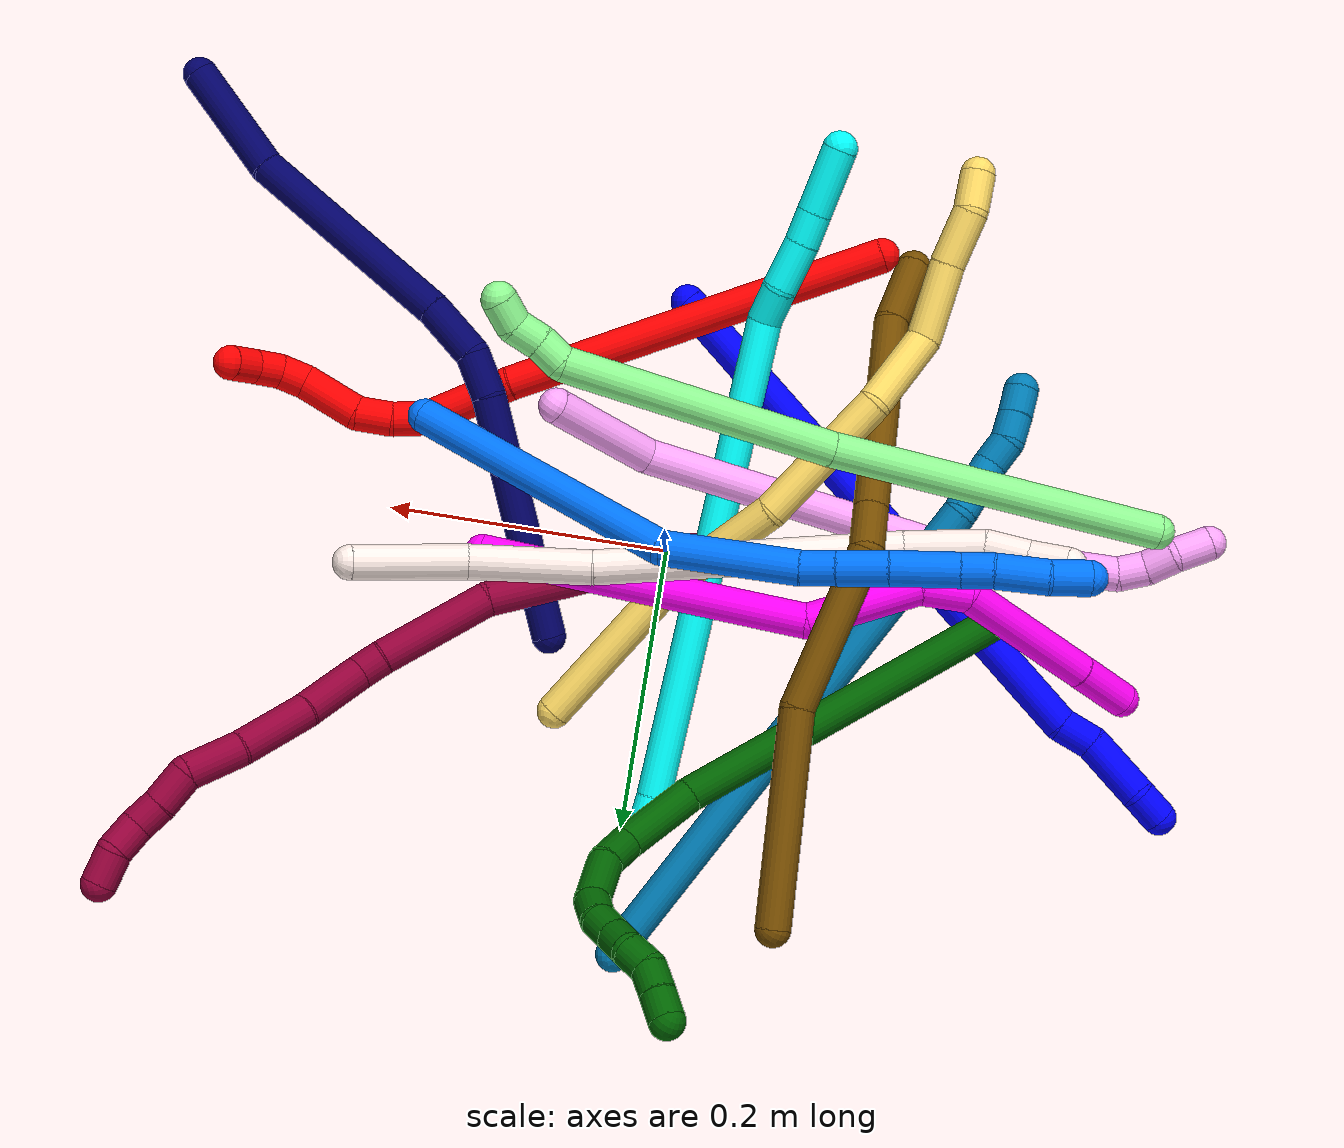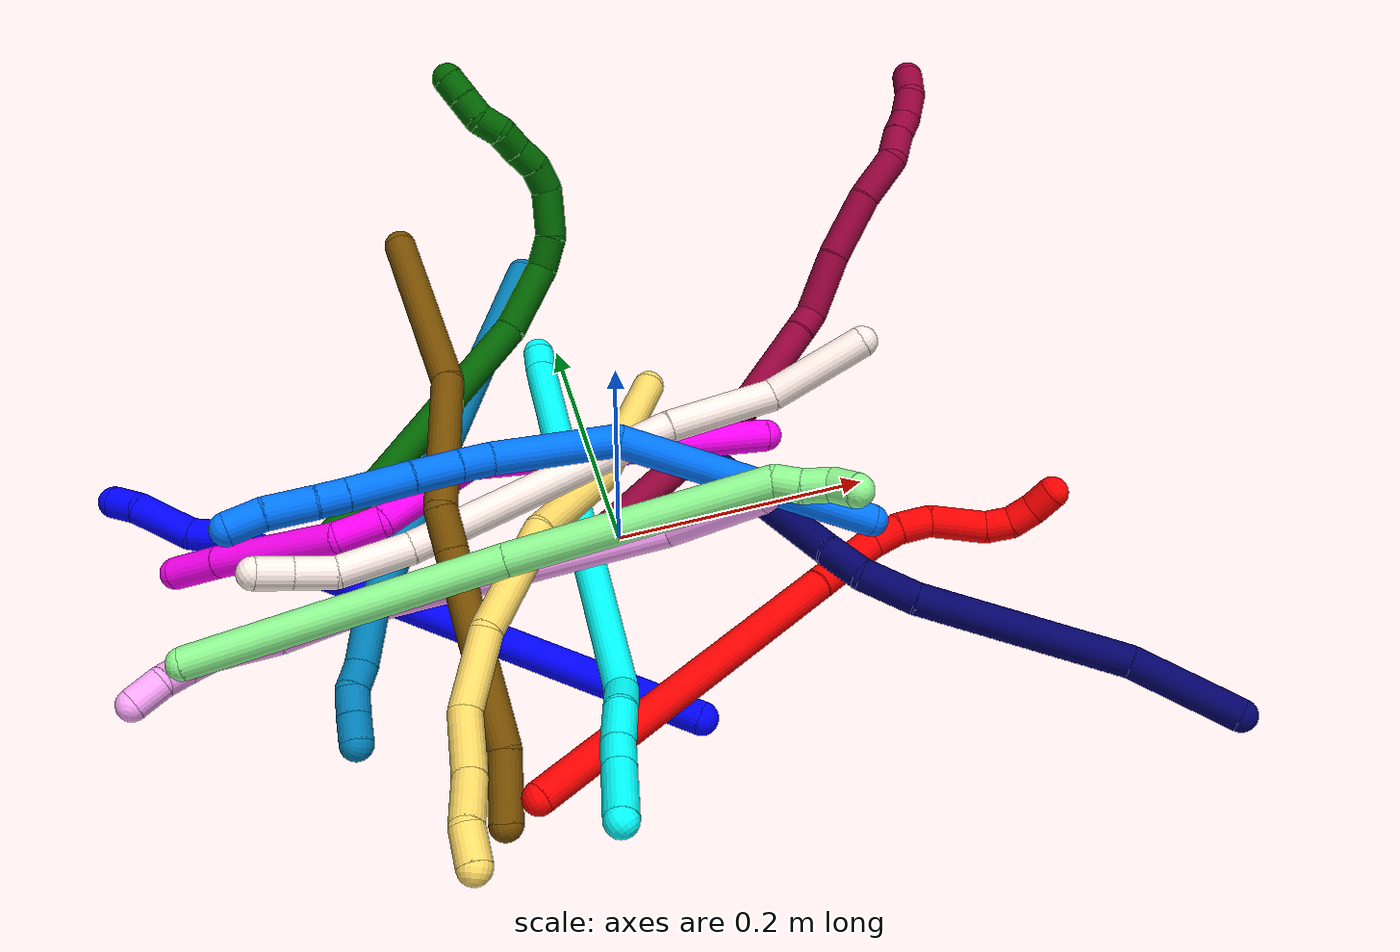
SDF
<sdf version="1.7">
 <world name="default">
  <plugin name="TubeGeneratorPlugin" filename="libtube_generator_plugin.so"/>
  <model name="photoneo_s_sensor">
   <static>1</static>
   <pose>0 0 2 1.57079 1.57079 3.14159</pose>
   <link name="link">
    <inertial><mass>0.1</mass></inertial>
    <sensor name="sensor" type="depth">
     <update_rate>30</update_rate>
     <camera>
      <horizontal_fov>1.22</horizontal_fov>
      <image><width>1920</width><height>1200</height><format>B8G8R8</format></image>
      <clip><near>0.1</near><far>4</far></clip>
      <depth_camera><output>points</output></depth_camera>
     </camera>
     <plugin name="camera_plugin" filename="libgazebo_ros_depth_camera.so">
      <baseline>0.2</baseline>
      <alwaysOn>1</alwaysOn>
      <updateRate>0.0</updateRate>
      <cameraName>camera_ir</cameraName>
      <imageTopicName>/camera/color/image_raw</imageTopicName>
      <cameraInfoTopicName>/camera/color/camera_info</cameraInfoTopicName>
      <depthImageTopicName>/camera/depth/image_raw</depthImageTopicName>
      <depthImageCameraInfoTopicName>/camera/depth/camera_info</depthImageCameraInfoTopicName>
      <pointCloudTopicName>/camera/depth/points</pointCloudTopicName>
      <frameName>fr_optical</frameName>
      <pointCloudCutoff>0.1</pointCloudCutoff>
      <pointCloudCutoffMax>2.0</pointCloudCutoffMax>
      <distortionK1>0</distortionK1>
      <distortionK2>0</distortionK2>
      <distortionK3>0</distortionK3>
      <distortionT1>0</distortionT1>
      <distortionT2>0</distortionT2>
      <CxPrime>0</CxPrime>
      <Cx>0</Cx>
      <Cy>0</Cy>
      <focalLength>0</focalLength>
      <hackBaseline>0</hackBaseline>
     </plugin>
    </sensor>
   </link>
  </model>
  <gravity>0 0 -9.8</gravity>
  <magnetic_field>6e-06 2.3e-05 -4.2e-05</magnetic_field>
  <atmosphere type="adiabatic"/>
  <physics name="default_physics" default="0" type="ode">
   <max_step_size>0.003</max_step_size>
   <real_time_factor>1</real_time_factor>
   <real_time_update_rate>1000</real_time_update_rate>
   <max_contacts>10000</max_contacts>
   <ode>
    <solver>
     <type>quick</type>
     <iters>100</iters>
     <sor>1.3</sor>
     <use_dynamic_moi_rescaling>0</use_dynamic_moi_rescaling>
    </solver>
    <constraints>
     <contact_max_correcting_vel>0</contact_max_correcting_vel>
     <contact_surface_layer>0.001</contact_surface_layer>
     <cfm>0</cfm>
     <erp>0.2</erp>
    </constraints>
   </ode>
  </physics>
  <scene><ambient>0.4 0.4 0.4 1</ambient><background>0.7 0.7 0.7 1</background><shadows>0</shadows></scene>
  <audio><device>default</device></audio>
  <spherical_coordinates>
   <surface_model>EARTH_WGS84</surface_model>
   <latitude_deg>0</latitude_deg>
   <longitude_deg>0</longitude_deg>
   <elevation>0</elevation>
   <heading_deg>0</heading_deg>
  </spherical_coordinates>
  <model name="bin">
   <static>1</static>
   <link name="bottom">
    <collision name="collision-bottom">
     <pose>0 0 -0.01 0 -0 0</pose>
     <geometry><box><size>0.8 0.6 0.02</size></box></geometry>
     <surface>
      <friction><ode><mu>100</mu><mu2>100</mu2></ode></friction>
      <contact><collide_bitmask>65535</collide_bitmask></contact>
     </surface>
    </collision>
   </link>
   <link name="west_wall">
    <collision name="collision-west_wall">
     <pose>-0.41 0 0.1 0 -0 0</pose>
     <geometry><box><size>0.02 0.6 0.2</size></box></geometry>
     <surface>
      <friction><ode><mu>100</mu><mu2>100</mu2></ode></friction>
      <contact><collide_bitmask>65535</collide_bitmask></contact>
     </surface>
    </collision>
   </link>
   <link name="east_wall">
    <collision name="collision-east_wall">
     <pose>0.41 0 0.1 0 -0 0</pose>
     <geometry><box><size>0.02 0.6 0.2</size></box></geometry>
     <surface>
      <friction><ode><mu>100</mu><mu2>100</mu2></ode></friction>
      <contact><collide_bitmask>65535</collide_bitmask></contact>
     </surface>
    </collision>
   </link>
   <link name="south_wall">
    <collision name="collision-south_wall">
     <pose>0 -0.31 0.1 0 -0 0</pose>
     <geometry><box><size>0.8 0.02 0.2</size></box></geometry>
     <surface>
      <friction><ode><mu>100</mu><mu2>100</mu2></ode></friction>
      <contact><collide_bitmask>65535</collide_bitmask></contact>
     </surface>
    </collision>
   </link>
   <link name="north_wall">
    <collision name="collision-north_wall">
     <pose>0 0.31 0.1 0 -0 0</pose>
     <geometry><box><size>0.8 0.02 0.2</size></box></geometry>
     <surface>
      <friction><ode><mu>100</mu><mu2>100</mu2></ode></friction>
      <contact><collide_bitmask>65535</collide_bitmask></contact>
     </surface>
    </collision>
   </link>
  </model>
  <model name="1">
   <static>0</static>
   <link name="1">
    <collision name="collision-cylinder-e_1_1_4">
     <pose>-0.05574 0.05105 0.09862 -0.477664 -0.465198 0.115226</pose>
     <geometry><cylinder><radius>0.0125</radius><length>0.248507</length></cylinder></geometry>
     <surface>
      <friction><ode><mu>1.16</mu><mu2>1.16</mu2><slip1>0</slip1><slip2>0</slip2></ode></friction>
      <contact><ode><kp>1e+06</kp><kd>1</kd><max_vel>0</max_vel><min_depth>0.001</min_depth></ode></contact>
     </surface>
    </collision>
    <visual name="visual-cylinder-e_1_1_4">
     <pose>-0.05574 0.05105 0.09862 -0.477664 -0.465198 0.115226</pose>
     <geometry><cylinder><radius>0.0125</radius><length>0.248507</length></cylinder></geometry>
     <material><ambient>0 0 1 1</ambient></material>
    </visual>
    <collision name="collision-cylinder-e_2_4_5">
     <pose>-0.145271 0.134293 0.258834 -0.481615 -0.452544 0.112948</pose>
     <geometry><cylinder><radius>0.0125</radius><length>0.15456</length></cylinder></geometry>
     <surface>
      <friction><ode><mu>1.16</mu><mu2>1.16</mu2><slip1>0</slip1><slip2>0</slip2></ode></friction>
      <contact><ode><kp>1e+06</kp><kd>1</kd><max_vel>0</max_vel><min_depth>0.001</min_depth></ode></contact>
     </surface>
    </collision>
    <visual name="visual-cylinder-e_2_4_5">
     <pose>-0.145271 0.134293 0.258834 -0.481615 -0.452544 0.112948</pose>
     <geometry><cylinder><radius>0.0125</radius><length>0.15456</length></cylinder></geometry>
     <material><ambient>0 0 1 1</ambient></material>
    </visual>
    <collision name="collision-cylinder-e_3_5_6">
     <pose>-0.18459 0.175189 0.32842 -0.827985 -0.437646 0.194806</pose>
     <geometry><cylinder><radius>0.0125</radius><length>0.026087</length></cylinder></geometry>
     <surface>
      <friction><ode><mu>1.16</mu><mu2>1.16</mu2><slip1>0</slip1><slip2>0</slip2></ode></friction>
      <contact><ode><kp>1e+06</kp><kd>1</kd><max_vel>0</max_vel><min_depth>0.001</min_depth></ode></contact>
     </surface>
    </collision>
    <visual name="visual-cylinder-e_3_5_6">
     <pose>-0.18459 0.175189 0.32842 -0.827985 -0.437646 0.194806</pose>
     <geometry><cylinder><radius>0.0125</radius><length>0.026087</length></cylinder></geometry>
     <material><ambient>0 0 1 1</ambient></material>
    </visual>
    <collision name="collision-cylinder-e_4_6_7">
     <pose>-0.204074 0.192638 0.353924 -0.463214 -0.619327 0.150631</pose>
     <geometry><cylinder><radius>0.0125</radius><length>0.048083</length></cylinder></geometry>
     <surface>
      <friction><ode><mu>1.16</mu><mu2>1.16</mu2><slip1>0</slip1><slip2>0</slip2></ode></friction>
      <contact><ode><kp>1e+06</kp><kd>1</kd><max_vel>0</max_vel><min_depth>0.001</min_depth></ode></contact>
     </surface>
    </collision>
    <visual name="visual-cylinder-e_4_6_7">
     <pose>-0.204074 0.192638 0.353924 -0.463214 -0.619327 0.150631</pose>
     <geometry><cylinder><radius>0.0125</radius><length>0.048083</length></cylinder></geometry>
     <material><ambient>0 0 1 1</ambient></material>
    </visual>
    <collision name="collision-cylinder-e_5_7_2">
     <pose>-0.221246 0.206657 0.380998 -0.503953 -0.286468 0.074225</pose>
     <geometry><cylinder><radius>0.0125</radius><length>0.022764</length></cylinder></geometry>
     <surface>
      <friction><ode><mu>1.16</mu><mu2>1.16</mu2><slip1>0</slip1><slip2>0</slip2></ode></friction>
      <contact><ode><kp>1e+06</kp><kd>1</kd><max_vel>0</max_vel><min_depth>0.001</min_depth></ode></contact>
     </surface>
    </collision>
    <visual name="visual-cylinder-e_5_7_2">
     <pose>-0.221246 0.206657 0.380998 -0.503953 -0.286468 0.074225</pose>
     <geometry><cylinder><radius>0.0125</radius><length>0.022764</length></cylinder></geometry>
     <material><ambient>0 0 1 1</ambient></material>
    </visual>
    <collision name="collision-sphere-2">
     <pose>-0.224462 0.21193 0.390558 0 -0 0</pose>
     <geometry><sphere><radius>0.0125</radius></sphere></geometry>
     <surface>
      <friction><ode><mu>1.16</mu><mu2>1.16</mu2><slip1>0</slip1><slip2>0</slip2></ode></friction>
      <contact><ode><kp>1e+06</kp><kd>1</kd><max_vel>0</max_vel><min_depth>0.001</min_depth></ode></contact>
     </surface>
    </collision>
    <visual name="visual-sphere-2">
     <pose>-0.224462 0.21193 0.390558 0 -0 0</pose>
     <geometry><sphere><radius>0.0125</radius></sphere></geometry>
     <material><ambient>0 0 1 1</ambient></material>
    </visual>
    <collision name="collision-sphere-7">
     <pose>-0.21803 0.201385 0.371437 0 -0 0</pose>
     <geometry><sphere><radius>0.0125</radius></sphere></geometry>
     <surface>
      <friction><ode><mu>1.16</mu><mu2>1.16</mu2><slip1>0</slip1><slip2>0</slip2></ode></friction>
      <contact><ode><kp>1e+06</kp><kd>1</kd><max_vel>0</max_vel><min_depth>0.001</min_depth></ode></contact>
     </surface>
    </collision>
    <visual name="visual-sphere-7">
     <pose>-0.21803 0.201385 0.371437 0 -0 0</pose>
     <geometry><sphere><radius>0.0125</radius></sphere></geometry>
     <material><ambient>0 0 1 1</ambient></material>
    </visual>
    <collision name="collision-sphere-6">
     <pose>-0.190118 0.183891 0.33641 0 -0 0</pose>
     <geometry><sphere><radius>0.0125</radius></sphere></geometry>
     <surface>
      <friction><ode><mu>1.16</mu><mu2>1.16</mu2><slip1>0</slip1><slip2>0</slip2></ode></friction>
      <contact><ode><kp>1e+06</kp><kd>1</kd><max_vel>0</max_vel><min_depth>0.001</min_depth></ode></contact>
     </surface>
    </collision>
    <visual name="visual-sphere-6">
     <pose>-0.190118 0.183891 0.33641 0 -0 0</pose>
     <geometry><sphere><radius>0.0125</radius></sphere></geometry>
     <material><ambient>0 0 1 1</ambient></material>
    </visual>
    <collision name="collision-sphere-5">
     <pose>-0.179062 0.166487 0.320429 0 -0 0</pose>
     <geometry><sphere><radius>0.0125</radius></sphere></geometry>
     <surface>
      <friction><ode><mu>1.16</mu><mu2>1.16</mu2><slip1>0</slip1><slip2>0</slip2></ode></friction>
      <contact><ode><kp>1e+06</kp><kd>1</kd><max_vel>0</max_vel><min_depth>0.001</min_depth></ode></contact>
     </surface>
    </collision>
    <visual name="visual-sphere-5">
     <pose>-0.179062 0.166487 0.320429 0 -0 0</pose>
     <geometry><sphere><radius>0.0125</radius></sphere></geometry>
     <material><ambient>0 0 1 1</ambient></material>
    </visual>
    <collision name="collision-sphere-1">
     <geometry><sphere><radius>0.0125</radius></sphere></geometry>
     <surface>
      <friction><ode><mu>1.16</mu><mu2>1.16</mu2><slip1>0</slip1><slip2>0</slip2></ode></friction>
      <contact><ode><kp>1e+06</kp><kd>1</kd><max_vel>0</max_vel><min_depth>0.001</min_depth></ode></contact>
     </surface>
    </collision>
    <visual name="visual-sphere-1">
     <geometry><sphere><radius>0.0125</radius></sphere></geometry>
     <material><ambient>0 0 1 1</ambient></material>
    </visual>
    <collision name="collision-sphere-4">
     <pose>-0.11148 0.1021 0.197239 0 -0 0</pose>
     <geometry><sphere><radius>0.0125</radius></sphere></geometry>
     <surface>
      <friction><ode><mu>1.16</mu><mu2>1.16</mu2><slip1>0</slip1><slip2>0</slip2></ode></friction>
      <contact><ode><kp>1e+06</kp><kd>1</kd><max_vel>0</max_vel><min_depth>0.001</min_depth></ode></contact>
     </surface>
    </collision>
    <visual name="visual-sphere-4">
     <pose>-0.11148 0.1021 0.197239 0 -0 0</pose>
     <geometry><sphere><radius>0.0125</radius></sphere></geometry>
     <material><ambient>0 0 1 1</ambient></material>
    </visual>
    <inertial>
     <pose>-0.111938 0.103959 0.197542 0 -0 0</pose>
     <mass>0.5</mass>
     <inertia>
      <ixx>0.001586</ixx>
      <ixy>0</ixy>
      <ixz>0</ixz>
      <iyy>0.001647</iyy>
      <iyz>0</iyz>
      <izz>8.7e-05</izz>
     </inertia>
    </inertial>
   </link>
   <pose>0.012641 -0.180085 0.012004 -2.63543 1.10962 -0.668973</pose>
  </model>
  <model name="2">
   <static>0</static>
   <link name="2">
    <collision name="collision-cylinder-e_1_1_4">
     <pose>0.068239 0.036273 0.116521 -0.301792 0.509854 -0.079207</pose>
     <geometry><cylinder><radius>0.0125</radius><length>0.279639</length></cylinder></geometry>
     <surface>
      <friction><ode><mu>1.16</mu><mu2>1.16</mu2><slip1>0</slip1><slip2>0</slip2></ode></friction>
      <contact><ode><kp>1e+06</kp><kd>1</kd><max_vel>0</max_vel><min_depth>0.001</min_depth></ode></contact>
     </surface>
    </collision>
    <visual name="visual-cylinder-e_1_1_4">
     <pose>0.068239 0.036273 0.116521 -0.301792 0.509854 -0.079207</pose>
     <geometry><cylinder><radius>0.0125</radius><length>0.279639</length></cylinder></geometry>
     <material><ambient>1 0 0 1</ambient></material>
    </visual>
    <collision name="collision-cylinder-e_2_4_5">
     <pose>0.155263 0.082108 0.258052 -0.365177 0.611788 -0.116492</pose>
     <geometry><cylinder><radius>0.0125</radius><length>0.065416</length></cylinder></geometry>
     <surface>
      <friction><ode><mu>1.16</mu><mu2>1.16</mu2><slip1>0</slip1><slip2>0</slip2></ode></friction>
      <contact><ode><kp>1e+06</kp><kd>1</kd><max_vel>0</max_vel><min_depth>0.001</min_depth></ode></contact>
     </surface>
    </collision>
    <visual name="visual-cylinder-e_2_4_5">
     <pose>0.155263 0.082108 0.258052 -0.365177 0.611788 -0.116492</pose>
     <geometry><cylinder><radius>0.0125</radius><length>0.065416</length></cylinder></geometry>
     <material><ambient>1 0 0 1</ambient></material>
    </visual>
    <collision name="collision-cylinder-e_3_5_6">
     <pose>0.177439 0.091984 0.295327 -0.025599 0.269648 -0.003473</pose>
     <geometry><cylinder><radius>0.0125</radius><length>0.025458</length></cylinder></geometry>
     <surface>
      <friction><ode><mu>1.16</mu><mu2>1.16</mu2><slip1>0</slip1><slip2>0</slip2></ode></friction>
      <contact><ode><kp>1e+06</kp><kd>1</kd><max_vel>0</max_vel><min_depth>0.001</min_depth></ode></contact>
     </surface>
    </collision>
    <visual name="visual-cylinder-e_3_5_6">
     <pose>0.177439 0.091984 0.295327 -0.025599 0.269648 -0.003473</pose>
     <geometry><cylinder><radius>0.0125</radius><length>0.025458</length></cylinder></geometry>
     <material><ambient>1 0 0 1</ambient></material>
    </visual>
    <collision name="collision-cylinder-e_4_6_7">
     <pose>0.185185 0.089622 0.319383 0.223194 0.345761 0.039132</pose>
     <geometry><cylinder><radius>0.0125</radius><length>0.025704</length></cylinder></geometry>
     <surface>
      <friction><ode><mu>1.16</mu><mu2>1.16</mu2><slip1>0</slip1><slip2>0</slip2></ode></friction>
      <contact><ode><kp>1e+06</kp><kd>1</kd><max_vel>0</max_vel><min_depth>0.001</min_depth></ode></contact>
     </surface>
    </collision>
    <visual name="visual-cylinder-e_4_6_7">
     <pose>0.185185 0.089622 0.319383 0.223194 0.345761 0.039132</pose>
     <geometry><cylinder><radius>0.0125</radius><length>0.025704</length></cylinder></geometry>
     <material><ambient>1 0 0 1</ambient></material>
    </visual>
    <collision name="collision-cylinder-e_5_7_8">
     <pose>0.196237 0.074652 0.347981 0.631559 0.311137 0.102391</pose>
     <geometry><cylinder><radius>0.0125</radius><length>0.043747</length></cylinder></geometry>
     <surface>
      <friction><ode><mu>1.16</mu><mu2>1.16</mu2><slip1>0</slip1><slip2>0</slip2></ode></friction>
      <contact><ode><kp>1e+06</kp><kd>1</kd><max_vel>0</max_vel><min_depth>0.001</min_depth></ode></contact>
     </surface>
    </collision>
    <visual name="visual-cylinder-e_5_7_8">
     <pose>0.196237 0.074652 0.347981 0.631559 0.311137 0.102391</pose>
     <geometry><cylinder><radius>0.0125</radius><length>0.043747</length></cylinder></geometry>
     <material><ambient>1 0 0 1</ambient></material>
    </visual>
    <collision name="collision-cylinder-e_6_8_9">
     <pose>0.203868 0.05868 0.374059 0.377615 0.093424 0.017864</pose>
     <geometry><cylinder><radius>0.0125</radius><length>0.020036</length></cylinder></geometry>
     <surface>
      <friction><ode><mu>1.16</mu><mu2>1.16</mu2><slip1>0</slip1><slip2>0</slip2></ode></friction>
      <contact><ode><kp>1e+06</kp><kd>1</kd><max_vel>0</max_vel><min_depth>0.001</min_depth></ode></contact>
     </surface>
    </collision>
    <visual name="visual-cylinder-e_6_8_9">
     <pose>0.203868 0.05868 0.374059 0.377615 0.093424 0.017864</pose>
     <geometry><cylinder><radius>0.0125</radius><length>0.020036</length></cylinder></geometry>
     <material><ambient>1 0 0 1</ambient></material>
    </visual>
    <collision name="collision-cylinder-e_7_9_10">
     <pose>0.203281 0.054202 0.393182 0.081025 -0.152789 -0.006205</pose>
     <geometry><cylinder><radius>0.0125</radius><length>0.02</length></cylinder></geometry>
     <surface>
      <friction><ode><mu>1.16</mu><mu2>1.16</mu2><slip1>0</slip1><slip2>0</slip2></ode></friction>
      <contact><ode><kp>1e+06</kp><kd>1</kd><max_vel>0</max_vel><min_depth>0.001</min_depth></ode></contact>
     </surface>
    </collision>
    <visual name="visual-cylinder-e_7_9_10">
     <pose>0.203281 0.054202 0.393182 0.081025 -0.152789 -0.006205</pose>
     <geometry><cylinder><radius>0.0125</radius><length>0.02</length></cylinder></geometry>
     <material><ambient>1 0 0 1</ambient></material>
    </visual>
    <collision name="collision-cylinder-e_8_10_2">
     <pose>0.198322 0.053468 0.412424 -0.007014 -0.350813 0.001243</pose>
     <geometry><cylinder><radius>0.0125</radius><length>0.020001</length></cylinder></geometry>
     <surface>
      <friction><ode><mu>1.16</mu><mu2>1.16</mu2><slip1>0</slip1><slip2>0</slip2></ode></friction>
      <contact><ode><kp>1e+06</kp><kd>1</kd><max_vel>0</max_vel><min_depth>0.001</min_depth></ode></contact>
     </surface>
    </collision>
    <visual name="visual-cylinder-e_8_10_2">
     <pose>0.198322 0.053468 0.412424 -0.007014 -0.350813 0.001243</pose>
     <geometry><cylinder><radius>0.0125</radius><length>0.020001</length></cylinder></geometry>
     <material><ambient>1 0 0 1</ambient></material>
    </visual>
    <collision name="collision-sphere-2">
     <pose>0.194885 0.053534 0.421815 0 -0 0</pose>
     <geometry><sphere><radius>0.0125</radius></sphere></geometry>
     <surface>
      <friction><ode><mu>1.16</mu><mu2>1.16</mu2><slip1>0</slip1><slip2>0</slip2></ode></friction>
      <contact><ode><kp>1e+06</kp><kd>1</kd><max_vel>0</max_vel><min_depth>0.001</min_depth></ode></contact>
     </surface>
    </collision>
    <visual name="visual-sphere-2">
     <pose>0.194885 0.053534 0.421815 0 -0 0</pose>
     <geometry><sphere><radius>0.0125</radius></sphere></geometry>
     <material><ambient>1 0 0 1</ambient></material>
    </visual>
    <collision name="collision-sphere-10">
     <pose>0.201759 0.053402 0.403033 0 -0 0</pose>
     <geometry><sphere><radius>0.0125</radius></sphere></geometry>
     <surface>
      <friction><ode><mu>1.16</mu><mu2>1.16</mu2><slip1>0</slip1><slip2>0</slip2></ode></friction>
      <contact><ode><kp>1e+06</kp><kd>1</kd><max_vel>0</max_vel><min_depth>0.001</min_depth></ode></contact>
     </surface>
    </collision>
    <visual name="visual-sphere-10">
     <pose>0.201759 0.053402 0.403033 0 -0 0</pose>
     <geometry><sphere><radius>0.0125</radius></sphere></geometry>
     <material><ambient>1 0 0 1</ambient></material>
    </visual>
    <collision name="collision-sphere-9">
     <pose>0.204803 0.055002 0.383331 0 -0 0</pose>
     <geometry><sphere><radius>0.0125</radius></sphere></geometry>
     <surface>
      <friction><ode><mu>1.16</mu><mu2>1.16</mu2><slip1>0</slip1><slip2>0</slip2></ode></friction>
      <contact><ode><kp>1e+06</kp><kd>1</kd><max_vel>0</max_vel><min_depth>0.001</min_depth></ode></contact>
     </surface>
    </collision>
    <visual name="visual-sphere-9">
     <pose>0.204803 0.055002 0.383331 0 -0 0</pose>
     <geometry><sphere><radius>0.0125</radius></sphere></geometry>
     <material><ambient>1 0 0 1</ambient></material>
    </visual>
    <collision name="collision-sphere-4">
     <pose>0.136478 0.072546 0.233042 0 -0 0</pose>
     <geometry><sphere><radius>0.0125</radius></sphere></geometry>
     <surface>
      <friction><ode><mu>1.16</mu><mu2>1.16</mu2><slip1>0</slip1><slip2>0</slip2></ode></friction>
      <contact><ode><kp>1e+06</kp><kd>1</kd><max_vel>0</max_vel><min_depth>0.001</min_depth></ode></contact>
     </surface>
    </collision>
    <visual name="visual-sphere-4">
     <pose>0.136478 0.072546 0.233042 0 -0 0</pose>
     <geometry><sphere><radius>0.0125</radius></sphere></geometry>
     <material><ambient>1 0 0 1</ambient></material>
    </visual>
    <collision name="collision-sphere-1">
     <geometry><sphere><radius>0.0125</radius></sphere></geometry>
     <surface>
      <friction><ode><mu>1.16</mu><mu2>1.16</mu2><slip1>0</slip1><slip2>0</slip2></ode></friction>
      <contact><ode><kp>1e+06</kp><kd>1</kd><max_vel>0</max_vel><min_depth>0.001</min_depth></ode></contact>
     </surface>
    </collision>
    <visual name="visual-sphere-1">
     <geometry><sphere><radius>0.0125</radius></sphere></geometry>
     <material><ambient>1 0 0 1</ambient></material>
    </visual>
    <collision name="collision-sphere-8">
     <pose>0.202934 0.062358 0.364788 0 -0 0</pose>
     <geometry><sphere><radius>0.0125</radius></sphere></geometry>
     <surface>
      <friction><ode><mu>1.16</mu><mu2>1.16</mu2><slip1>0</slip1><slip2>0</slip2></ode></friction>
      <contact><ode><kp>1e+06</kp><kd>1</kd><max_vel>0</max_vel><min_depth>0.001</min_depth></ode></contact>
     </surface>
    </collision>
    <visual name="visual-sphere-8">
     <pose>0.202934 0.062358 0.364788 0 -0 0</pose>
     <geometry><sphere><radius>0.0125</radius></sphere></geometry>
     <material><ambient>1 0 0 1</ambient></material>
    </visual>
    <collision name="collision-sphere-5">
     <pose>0.174048 0.09167 0.283062 0 -0 0</pose>
     <geometry><sphere><radius>0.0125</radius></sphere></geometry>
     <surface>
      <friction><ode><mu>1.16</mu><mu2>1.16</mu2><slip1>0</slip1><slip2>0</slip2></ode></friction>
      <contact><ode><kp>1e+06</kp><kd>1</kd><max_vel>0</max_vel><min_depth>0.001</min_depth></ode></contact>
     </surface>
    </collision>
    <visual name="visual-sphere-5">
     <pose>0.174048 0.09167 0.283062 0 -0 0</pose>
     <geometry><sphere><radius>0.0125</radius></sphere></geometry>
     <material><ambient>1 0 0 1</ambient></material>
    </visual>
    <collision name="collision-sphere-6">
     <pose>0.18083 0.092298 0.307592 0 -0 0</pose>
     <geometry><sphere><radius>0.0125</radius></sphere></geometry>
     <surface>
      <friction><ode><mu>1.16</mu><mu2>1.16</mu2><slip1>0</slip1><slip2>0</slip2></ode></friction>
      <contact><ode><kp>1e+06</kp><kd>1</kd><max_vel>0</max_vel><min_depth>0.001</min_depth></ode></contact>
     </surface>
    </collision>
    <visual name="visual-sphere-6">
     <pose>0.18083 0.092298 0.307592 0 -0 0</pose>
     <geometry><sphere><radius>0.0125</radius></sphere></geometry>
     <material><ambient>1 0 0 1</ambient></material>
    </visual>
    <collision name="collision-sphere-7">
     <pose>0.189541 0.086946 0.331175 0 -0 0</pose>
     <geometry><sphere><radius>0.0125</radius></sphere></geometry>
     <surface>
      <friction><ode><mu>1.16</mu><mu2>1.16</mu2><slip1>0</slip1><slip2>0</slip2></ode></friction>
      <contact><ode><kp>1e+06</kp><kd>1</kd><max_vel>0</max_vel><min_depth>0.001</min_depth></ode></contact>
     </surface>
    </collision>
    <visual name="visual-sphere-7">
     <pose>0.189541 0.086946 0.331175 0 -0 0</pose>
     <geometry><sphere><radius>0.0125</radius></sphere></geometry>
     <material><ambient>1 0 0 1</ambient></material>
    </visual>
    <inertial>
     <pose>0.118436 0.05351 0.208045 0 -0 0</pose>
     <mass>0.5</mass>
     <inertia>
      <ixx>0.00152</ixx>
      <ixy>0</ixy>
      <ixz>0</ixz>
      <iyy>0.001683</iyy>
      <iyz>0</iyz>
      <izz>-0.001357</izz>
     </inertia>
    </inertial>
   </link>
   <pose>-0.118764 -0.229082 0.047534 0.280847 1.14586 0.46319</pose>
  </model>
  <model name="3">
   <static>0</static>
   <link name="3">
    <collision name="collision-cylinder-e_1_1_4">
     <pose>-0.002943 -0.005253 -0.008058 2.56393 -0.296863 -0.932469</pose>
     <geometry><cylinder><radius>0.0125</radius><length>0.020118</length></cylinder></geometry>
     <surface>
      <friction><ode><mu>1.16</mu><mu2>1.16</mu2><slip1>0</slip1><slip2>0</slip2></ode></friction>
      <contact><ode><kp>1e+06</kp><kd>1</kd><max_vel>0</max_vel><min_depth>0.001</min_depth></ode></contact>
     </surface>
    </collision>
    <visual name="visual-cylinder-e_1_1_4">
     <pose>-0.002943 -0.005253 -0.008058 2.56393 -0.296863 -0.932469</pose>
     <geometry><cylinder><radius>0.0125</radius><length>0.020118</length></cylinder></geometry>
     <material><ambient>0.003922 1 0.996078 1</ambient></material>
    </visual>
    <collision name="collision-cylinder-e_2_4_5">
     <pose>-0.035007 -0.118541 -0.14848 2.45705 -0.168824 -0.466321</pose>
     <geometry><cylinder><radius>0.0125</radius><length>0.34664</length></cylinder></geometry>
     <surface>
      <friction><ode><mu>1.16</mu><mu2>1.16</mu2><slip1>0</slip1><slip2>0</slip2></ode></friction>
      <contact><ode><kp>1e+06</kp><kd>1</kd><max_vel>0</max_vel><min_depth>0.001</min_depth></ode></contact>
     </surface>
    </collision>
    <visual name="visual-cylinder-e_2_4_5">
     <pose>-0.035007 -0.118541 -0.14848 2.45705 -0.168824 -0.466321</pose>
     <geometry><cylinder><radius>0.0125</radius><length>0.34664</length></cylinder></geometry>
     <material><ambient>0.003922 1 0.996078 1</ambient></material>
    </visual>
    <collision name="collision-cylinder-e_3_5_6">
     <pose>-0.06582 -0.238932 -0.286317 1.98786 -0.124471 -0.190954</pose>
     <geometry><cylinder><radius>0.0125</radius><length>0.027238</length></cylinder></geometry>
     <surface>
      <friction><ode><mu>1.16</mu><mu2>1.16</mu2><slip1>0</slip1><slip2>0</slip2></ode></friction>
      <contact><ode><kp>1e+06</kp><kd>1</kd><max_vel>0</max_vel><min_depth>0.001</min_depth></ode></contact>
     </surface>
    </collision>
    <visual name="visual-cylinder-e_3_5_6">
     <pose>-0.06582 -0.238932 -0.286317 1.98786 -0.124471 -0.190954</pose>
     <geometry><cylinder><radius>0.0125</radius><length>0.027238</length></cylinder></geometry>
     <material><ambient>0.003922 1 0.996078 1</ambient></material>
    </visual>
    <collision name="collision-cylinder-e_4_6_7">
     <pose>-0.072473 -0.264946 -0.301547 2.19103 -0.287503 -0.548372</pose>
     <geometry><cylinder><radius>0.0125</radius><length>0.035006</length></cylinder></geometry>
     <surface>
      <friction><ode><mu>1.16</mu><mu2>1.16</mu2><slip1>0</slip1><slip2>0</slip2></ode></friction>
      <contact><ode><kp>1e+06</kp><kd>1</kd><max_vel>0</max_vel><min_depth>0.001</min_depth></ode></contact>
     </surface>
    </collision>
    <visual name="visual-cylinder-e_4_6_7">
     <pose>-0.072473 -0.264946 -0.301547 2.19103 -0.287503 -0.548372</pose>
     <geometry><cylinder><radius>0.0125</radius><length>0.035006</length></cylinder></geometry>
     <material><ambient>0.003922 1 0.996078 1</ambient></material>
    </visual>
    <collision name="collision-cylinder-e_5_7_8">
     <pose>-0.079938 -0.287594 -0.318296 2.23191 -0.216197 -0.436741</pose>
     <geometry><cylinder><radius>0.0125</radius><length>0.023322</length></cylinder></geometry>
     <surface>
      <friction><ode><mu>1.16</mu><mu2>1.16</mu2><slip1>0</slip1><slip2>0</slip2></ode></friction>
      <contact><ode><kp>1e+06</kp><kd>1</kd><max_vel>0</max_vel><min_depth>0.001</min_depth></ode></contact>
     </surface>
    </collision>
    <visual name="visual-cylinder-e_5_7_8">
     <pose>-0.079938 -0.287594 -0.318296 2.23191 -0.216197 -0.436741</pose>
     <geometry><cylinder><radius>0.0125</radius><length>0.023322</length></cylinder></geometry>
     <material><ambient>0.003922 1 0.996078 1</ambient></material>
    </visual>
    <collision name="collision-cylinder-e_6_8_2">
     <pose>-0.087253 -0.315346 -0.339184 2.20823 -0.203319 -0.399569</pose>
     <geometry><cylinder><radius>0.0125</radius><length>0.047676</length></cylinder></geometry>
     <surface>
      <friction><ode><mu>1.16</mu><mu2>1.16</mu2><slip1>0</slip1><slip2>0</slip2></ode></friction>
      <contact><ode><kp>1e+06</kp><kd>1</kd><max_vel>0</max_vel><min_depth>0.001</min_depth></ode></contact>
     </surface>
    </collision>
    <visual name="visual-cylinder-e_6_8_2">
     <pose>-0.087253 -0.315346 -0.339184 2.20823 -0.203319 -0.399569</pose>
     <geometry><cylinder><radius>0.0125</radius><length>0.047676</length></cylinder></geometry>
     <material><ambient>0.003922 1 0.996078 1</ambient></material>
    </visual>
    <collision name="collision-sphere-2">
     <pose>-0.092066 -0.334108 -0.353078 0 -0 0</pose>
     <geometry><sphere><radius>0.0125</radius></sphere></geometry>
     <surface>
      <friction><ode><mu>1.16</mu><mu2>1.16</mu2><slip1>0</slip1><slip2>0</slip2></ode></friction>
      <contact><ode><kp>1e+06</kp><kd>1</kd><max_vel>0</max_vel><min_depth>0.001</min_depth></ode></contact>
     </surface>
    </collision>
    <visual name="visual-sphere-2">
     <pose>-0.092066 -0.334108 -0.353078 0 -0 0</pose>
     <geometry><sphere><radius>0.0125</radius></sphere></geometry>
     <material><ambient>0.003922 1 0.996078 1</ambient></material>
    </visual>
    <collision name="collision-sphere-4">
     <pose>-0.005885 -0.010505 -0.016117 0 -0 0</pose>
     <geometry><sphere><radius>0.0125</radius></sphere></geometry>
     <surface>
      <friction><ode><mu>1.16</mu><mu2>1.16</mu2><slip1>0</slip1><slip2>0</slip2></ode></friction>
      <contact><ode><kp>1e+06</kp><kd>1</kd><max_vel>0</max_vel><min_depth>0.001</min_depth></ode></contact>
     </surface>
    </collision>
    <visual name="visual-sphere-4">
     <pose>-0.005885 -0.010505 -0.016117 0 -0 0</pose>
     <geometry><sphere><radius>0.0125</radius></sphere></geometry>
     <material><ambient>0.003922 1 0.996078 1</ambient></material>
    </visual>
    <collision name="collision-sphere-1">
     <geometry><sphere><radius>0.0125</radius></sphere></geometry>
     <surface>
      <friction><ode><mu>1.16</mu><mu2>1.16</mu2><slip1>0</slip1><slip2>0</slip2></ode></friction>
      <contact><ode><kp>1e+06</kp><kd>1</kd><max_vel>0</max_vel><min_depth>0.001</min_depth></ode></contact>
     </surface>
    </collision>
    <visual name="visual-sphere-1">
     <geometry><sphere><radius>0.0125</radius></sphere></geometry>
     <material><ambient>0.003922 1 0.996078 1</ambient></material>
    </visual>
    <collision name="collision-sphere-8">
     <pose>-0.082439 -0.296584 -0.325289 0 -0 0</pose>
     <geometry><sphere><radius>0.0125</radius></sphere></geometry>
     <surface>
      <friction><ode><mu>1.16</mu><mu2>1.16</mu2><slip1>0</slip1><slip2>0</slip2></ode></friction>
      <contact><ode><kp>1e+06</kp><kd>1</kd><max_vel>0</max_vel><min_depth>0.001</min_depth></ode></contact>
     </surface>
    </collision>
    <visual name="visual-sphere-8">
     <pose>-0.082439 -0.296584 -0.325289 0 -0 0</pose>
     <geometry><sphere><radius>0.0125</radius></sphere></geometry>
     <material><ambient>0.003922 1 0.996078 1</ambient></material>
    </visual>
    <collision name="collision-sphere-5">
     <pose>-0.064129 -0.226577 -0.280843 0 -0 0</pose>
     <geometry><sphere><radius>0.0125</radius></sphere></geometry>
     <surface>
      <friction><ode><mu>1.16</mu><mu2>1.16</mu2><slip1>0</slip1><slip2>0</slip2></ode></friction>
      <contact><ode><kp>1e+06</kp><kd>1</kd><max_vel>0</max_vel><min_depth>0.001</min_depth></ode></contact>
     </surface>
    </collision>
    <visual name="visual-sphere-5">
     <pose>-0.064129 -0.226577 -0.280843 0 -0 0</pose>
     <geometry><sphere><radius>0.0125</radius></sphere></geometry>
     <material><ambient>0.003922 1 0.996078 1</ambient></material>
    </visual>
    <collision name="collision-sphere-6">
     <pose>-0.06751 -0.251287 -0.291791 0 -0 0</pose>
     <geometry><sphere><radius>0.0125</radius></sphere></geometry>
     <surface>
      <friction><ode><mu>1.16</mu><mu2>1.16</mu2><slip1>0</slip1><slip2>0</slip2></ode></friction>
      <contact><ode><kp>1e+06</kp><kd>1</kd><max_vel>0</max_vel><min_depth>0.001</min_depth></ode></contact>
     </surface>
    </collision>
    <visual name="visual-sphere-6">
     <pose>-0.06751 -0.251287 -0.291791 0 -0 0</pose>
     <geometry><sphere><radius>0.0125</radius></sphere></geometry>
     <material><ambient>0.003922 1 0.996078 1</ambient></material>
    </visual>
    <collision name="collision-sphere-7">
     <pose>-0.077436 -0.278604 -0.311302 0 -0 0</pose>
     <geometry><sphere><radius>0.0125</radius></sphere></geometry>
     <surface>
      <friction><ode><mu>1.16</mu><mu2>1.16</mu2><slip1>0</slip1><slip2>0</slip2></ode></friction>
      <contact><ode><kp>1e+06</kp><kd>1</kd><max_vel>0</max_vel><min_depth>0.001</min_depth></ode></contact>
     </surface>
    </collision>
    <visual name="visual-sphere-7">
     <pose>-0.077436 -0.278604 -0.311302 0 -0 0</pose>
     <geometry><sphere><radius>0.0125</radius></sphere></geometry>
     <material><ambient>0.003922 1 0.996078 1</ambient></material>
    </visual>
    <inertial>
     <pose>-0.045096 -0.157442 -0.18716 0 -0 0</pose>
     <mass>0.5</mass>
     <inertia>
      <ixx>0.001527</ixx>
      <ixy>0</ixy>
      <ixz>0</ixz>
      <iyy>-0.003834</iyy>
      <iyz>0</iyz>
      <izz>0.002752</izz>
     </inertia>
    </inertial>
   </link>
   <pose>-0.017079 0.194224 0.011927 -1.12344 -0.469654 0.190009</pose>
  </model>
  <model name="4">
   <static>0</static>
   <link name="4">
    <collision name="collision-cylinder-e_1_1_4">
     <pose>-0.038042 0.011703 0.004093 -1.23431 -1.25575 0.951296</pose>
     <geometry><cylinder><radius>0.0125</radius><length>0.080023</length></cylinder></geometry>
     <surface>
      <friction><ode><mu>1.16</mu><mu2>1.16</mu2><slip1>0</slip1><slip2>0</slip2></ode></friction>
      <contact><ode><kp>1e+06</kp><kd>1</kd><max_vel>0</max_vel><min_depth>0.001</min_depth></ode></contact>
     </surface>
    </collision>
    <visual name="visual-cylinder-e_1_1_4">
     <pose>-0.038042 0.011703 0.004093 -1.23431 -1.25575 0.951296</pose>
     <geometry><cylinder><radius>0.0125</radius><length>0.080023</length></cylinder></geometry>
     <material><ambient>1 0.65098 0.996078 1</ambient></material>
    </visual>
    <collision name="collision-cylinder-e_2_4_5">
     <pose>-0.196132 0.02973 -0.013879 -2.86243 -1.38186 2.805</pose>
     <geometry><cylinder><radius>0.0125</radius><length>0.244445</length></cylinder></geometry>
     <surface>
      <friction><ode><mu>1.16</mu><mu2>1.16</mu2><slip1>0</slip1><slip2>0</slip2></ode></friction>
      <contact><ode><kp>1e+06</kp><kd>1</kd><max_vel>0</max_vel><min_depth>0.001</min_depth></ode></contact>
     </surface>
    </collision>
    <visual name="visual-cylinder-e_2_4_5">
     <pose>-0.196132 0.02973 -0.013879 -2.86243 -1.38186 2.805</pose>
     <geometry><cylinder><radius>0.0125</radius><length>0.244445</length></cylinder></geometry>
     <material><ambient>1 0.65098 0.996078 1</ambient></material>
    </visual>
    <collision name="collision-cylinder-e_3_5_6">
     <pose>-0.341814 0.037474 -0.04688 -3.0126 -1.16458 2.94604</pose>
     <geometry><cylinder><radius>0.0125</radius><length>0.05581</length></cylinder></geometry>
     <surface>
      <friction><ode><mu>1.16</mu><mu2>1.16</mu2><slip1>0</slip1><slip2>0</slip2></ode></friction>
      <contact><ode><kp>1e+06</kp><kd>1</kd><max_vel>0</max_vel><min_depth>0.001</min_depth></ode></contact>
     </surface>
    </collision>
    <visual name="visual-cylinder-e_3_5_6">
     <pose>-0.341814 0.037474 -0.04688 -3.0126 -1.16458 2.94604</pose>
     <geometry><cylinder><radius>0.0125</radius><length>0.05581</length></cylinder></geometry>
     <material><ambient>1 0.65098 0.996078 1</ambient></material>
    </visual>
    <collision name="collision-cylinder-e_4_6_7">
     <pose>-0.390676 0.037047 -0.067472 2.95278 -1.17039 -2.85772</pose>
     <geometry><cylinder><radius>0.0125</radius><length>0.050446</length></cylinder></geometry>
     <surface>
      <friction><ode><mu>1.16</mu><mu2>1.16</mu2><slip1>0</slip1><slip2>0</slip2></ode></friction>
      <contact><ode><kp>1e+06</kp><kd>1</kd><max_vel>0</max_vel><min_depth>0.001</min_depth></ode></contact>
     </surface>
    </collision>
    <visual name="visual-cylinder-e_4_6_7">
     <pose>-0.390676 0.037047 -0.067472 2.95278 -1.17039 -2.85772</pose>
     <geometry><cylinder><radius>0.0125</radius><length>0.050446</length></cylinder></geometry>
     <material><ambient>1 0.65098 0.996078 1</ambient></material>
    </visual>
    <collision name="collision-cylinder-e_5_7_8">
     <pose>-0.421708 0.03517 -0.084366 3.13721 -0.823065 -3.13155</pose>
     <geometry><cylinder><radius>0.0125</radius><length>0.021287</length></cylinder></geometry>
     <surface>
      <friction><ode><mu>1.16</mu><mu2>1.16</mu2><slip1>0</slip1><slip2>0</slip2></ode></friction>
      <contact><ode><kp>1e+06</kp><kd>1</kd><max_vel>0</max_vel><min_depth>0.001</min_depth></ode></contact>
     </surface>
    </collision>
    <visual name="visual-cylinder-e_5_7_8">
     <pose>-0.421708 0.03517 -0.084366 3.13721 -0.823065 -3.13155</pose>
     <geometry><cylinder><radius>0.0125</radius><length>0.021287</length></cylinder></geometry>
     <material><ambient>1 0.65098 0.996078 1</ambient></material>
    </visual>
    <collision name="collision-cylinder-e_6_8_9">
     <pose>-0.435061 0.033626 -0.101209 2.98543 -0.518519 -2.56786</pose>
     <geometry><cylinder><radius>0.0125</radius><length>0.02239</length></cylinder></geometry>
     <surface>
      <friction><ode><mu>1.16</mu><mu2>1.16</mu2><slip1>0</slip1><slip2>0</slip2></ode></friction>
      <contact><ode><kp>1e+06</kp><kd>1</kd><max_vel>0</max_vel><min_depth>0.001</min_depth></ode></contact>
     </surface>
    </collision>
    <visual name="visual-cylinder-e_6_8_9">
     <pose>-0.435061 0.033626 -0.101209 2.98543 -0.518519 -2.56786</pose>
     <geometry><cylinder><radius>0.0125</radius><length>0.02239</length></cylinder></geometry>
     <material><ambient>1 0.65098 0.996078 1</ambient></material>
    </visual>
    <collision name="collision-cylinder-e_7_9_2">
     <pose>-0.449307 0.034451 -0.119908 -2.89005 -0.747185 2.51757</pose>
     <geometry><cylinder><radius>0.0125</radius><length>0.025599</length></cylinder></geometry>
     <surface>
      <friction><ode><mu>1.16</mu><mu2>1.16</mu2><slip1>0</slip1><slip2>0</slip2></ode></friction>
      <contact><ode><kp>1e+06</kp><kd>1</kd><max_vel>0</max_vel><min_depth>0.001</min_depth></ode></contact>
     </surface>
    </collision>
    <visual name="visual-cylinder-e_7_9_2">
     <pose>-0.449307 0.034451 -0.119908 -2.89005 -0.747185 2.51757</pose>
     <geometry><cylinder><radius>0.0125</radius><length>0.025599</length></cylinder></geometry>
     <material><ambient>1 0.65098 0.996078 1</ambient></material>
    </visual>
    <collision name="collision-sphere-2">
     <pose>-0.458005 0.036788 -0.129002 0 -0 0</pose>
     <geometry><sphere><radius>0.0125</radius></sphere></geometry>
     <surface>
      <friction><ode><mu>1.16</mu><mu2>1.16</mu2><slip1>0</slip1><slip2>0</slip2></ode></friction>
      <contact><ode><kp>1e+06</kp><kd>1</kd><max_vel>0</max_vel><min_depth>0.001</min_depth></ode></contact>
     </surface>
    </collision>
    <visual name="visual-sphere-2">
     <pose>-0.458005 0.036788 -0.129002 0 -0 0</pose>
     <geometry><sphere><radius>0.0125</radius></sphere></geometry>
     <material><ambient>1 0.65098 0.996078 1</ambient></material>
    </visual>
    <collision name="collision-sphere-9">
     <pose>-0.440609 0.032114 -0.110814 0 -0 0</pose>
     <geometry><sphere><radius>0.0125</radius></sphere></geometry>
     <surface>
      <friction><ode><mu>1.16</mu><mu2>1.16</mu2><slip1>0</slip1><slip2>0</slip2></ode></friction>
      <contact><ode><kp>1e+06</kp><kd>1</kd><max_vel>0</max_vel><min_depth>0.001</min_depth></ode></contact>
     </surface>
    </collision>
    <visual name="visual-sphere-9">
     <pose>-0.440609 0.032114 -0.110814 0 -0 0</pose>
     <geometry><sphere><radius>0.0125</radius></sphere></geometry>
     <material><ambient>1 0.65098 0.996078 1</ambient></material>
    </visual>
    <collision name="collision-sphere-4">
     <pose>-0.076085 0.023405 0.008187 0 -0 0</pose>
     <geometry><sphere><radius>0.0125</radius></sphere></geometry>
     <surface>
      <friction><ode><mu>1.16</mu><mu2>1.16</mu2><slip1>0</slip1><slip2>0</slip2></ode></friction>
      <contact><ode><kp>1e+06</kp><kd>1</kd><max_vel>0</max_vel><min_depth>0.001</min_depth></ode></contact>
     </surface>
    </collision>
    <visual name="visual-sphere-4">
     <pose>-0.076085 0.023405 0.008187 0 -0 0</pose>
     <geometry><sphere><radius>0.0125</radius></sphere></geometry>
     <material><ambient>1 0.65098 0.996078 1</ambient></material>
    </visual>
    <collision name="collision-sphere-1">
     <geometry><sphere><radius>0.0125</radius></sphere></geometry>
     <surface>
      <friction><ode><mu>1.16</mu><mu2>1.16</mu2><slip1>0</slip1><slip2>0</slip2></ode></friction>
      <contact><ode><kp>1e+06</kp><kd>1</kd><max_vel>0</max_vel><min_depth>0.001</min_depth></ode></contact>
     </surface>
    </collision>
    <visual name="visual-sphere-1">
     <geometry><sphere><radius>0.0125</radius></sphere></geometry>
     <material><ambient>1 0.65098 0.996078 1</ambient></material>
    </visual>
    <collision name="collision-sphere-8">
     <pose>-0.429512 0.035138 -0.091603 0 -0 0</pose>
     <geometry><sphere><radius>0.0125</radius></sphere></geometry>
     <surface>
      <friction><ode><mu>1.16</mu><mu2>1.16</mu2><slip1>0</slip1><slip2>0</slip2></ode></friction>
      <contact><ode><kp>1e+06</kp><kd>1</kd><max_vel>0</max_vel><min_depth>0.001</min_depth></ode></contact>
     </surface>
    </collision>
    <visual name="visual-sphere-8">
     <pose>-0.429512 0.035138 -0.091603 0 -0 0</pose>
     <geometry><sphere><radius>0.0125</radius></sphere></geometry>
     <material><ambient>1 0.65098 0.996078 1</ambient></material>
    </visual>
    <collision name="collision-sphere-5">
     <pose>-0.31618 0.036056 -0.035946 0 -0 0</pose>
     <geometry><sphere><radius>0.0125</radius></sphere></geometry>
     <surface>
      <friction><ode><mu>1.16</mu><mu2>1.16</mu2><slip1>0</slip1><slip2>0</slip2></ode></friction>
      <contact><ode><kp>1e+06</kp><kd>1</kd><max_vel>0</max_vel><min_depth>0.001</min_depth></ode></contact>
     </surface>
    </collision>
    <visual name="visual-sphere-5">
     <pose>-0.31618 0.036056 -0.035946 0 -0 0</pose>
     <geometry><sphere><radius>0.0125</radius></sphere></geometry>
     <material><ambient>1 0.65098 0.996078 1</ambient></material>
    </visual>
    <collision name="collision-sphere-6">
     <pose>-0.367448 0.038892 -0.057815 0 -0 0</pose>
     <geometry><sphere><radius>0.0125</radius></sphere></geometry>
     <surface>
      <friction><ode><mu>1.16</mu><mu2>1.16</mu2><slip1>0</slip1><slip2>0</slip2></ode></friction>
      <contact><ode><kp>1e+06</kp><kd>1</kd><max_vel>0</max_vel><min_depth>0.001</min_depth></ode></contact>
     </surface>
    </collision>
    <visual name="visual-sphere-6">
     <pose>-0.367448 0.038892 -0.057815 0 -0 0</pose>
     <geometry><sphere><radius>0.0125</radius></sphere></geometry>
     <material><ambient>1 0.65098 0.996078 1</ambient></material>
    </visual>
    <collision name="collision-sphere-7">
     <pose>-0.413904 0.035202 -0.077129 0 -0 0</pose>
     <geometry><sphere><radius>0.0125</radius></sphere></geometry>
     <surface>
      <friction><ode><mu>1.16</mu><mu2>1.16</mu2><slip1>0</slip1><slip2>0</slip2></ode></friction>
      <contact><ode><kp>1e+06</kp><kd>1</kd><max_vel>0</max_vel><min_depth>0.001</min_depth></ode></contact>
     </surface>
    </collision>
    <visual name="visual-sphere-7">
     <pose>-0.413904 0.035202 -0.077129 0 -0 0</pose>
     <geometry><sphere><radius>0.0125</radius></sphere></geometry>
     <material><ambient>1 0.65098 0.996078 1</ambient></material>
    </visual>
    <inertial>
     <pose>-0.239984 0.029095 -0.032433 0 -0 0</pose>
     <mass>0.5</mass>
     <inertia>
      <ixx>-0.000172</ixx>
      <ixy>0</ixy>
      <ixz>0</ixz>
      <iyy>0.00139</iyy>
      <iyz>0</iyz>
      <izz>0.001192</izz>
     </inertia>
    </inertial>
   </link>
   <pose>0.087692 -0.078168 0.12106 -1.96924 -0.240291 -0.315661</pose>
  </model>
  <model name="5">
   <static>0</static>
   <link name="5">
    <collision name="collision-cylinder-e_1_1_4">
     <pose>-0.011305 -0.034766 0.048992 0.617166 -0.186009 -0.059447</pose>
     <geometry><cylinder><radius>0.0125</radius><length>0.122257</length></cylinder></geometry>
     <surface>
      <friction><ode><mu>1.16</mu><mu2>1.16</mu2><slip1>0</slip1><slip2>0</slip2></ode></friction>
      <contact><ode><kp>1e+06</kp><kd>1</kd><max_vel>0</max_vel><min_depth>0.001</min_depth></ode></contact>
     </surface>
    </collision>
    <visual name="visual-cylinder-e_1_1_4">
     <pose>-0.011305 -0.034766 0.048992 0.617166 -0.186009 -0.059447</pose>
     <geometry><cylinder><radius>0.0125</radius><length>0.122257</length></cylinder></geometry>
     <material><ambient>1 0.858824 0.4 1</ambient></material>
    </visual>
    <collision name="collision-cylinder-e_2_4_5">
     <pose>-0.027818 -0.104745 0.127252 0.877313 -0.113263 -0.05318</pose>
     <geometry><cylinder><radius>0.0125</radius><length>0.092167</length></cylinder></geometry>
     <surface>
      <friction><ode><mu>1.16</mu><mu2>1.16</mu2><slip1>0</slip1><slip2>0</slip2></ode></friction>
      <contact><ode><kp>1e+06</kp><kd>1</kd><max_vel>0</max_vel><min_depth>0.001</min_depth></ode></contact>
     </surface>
    </collision>
    <visual name="visual-cylinder-e_2_4_5">
     <pose>-0.027818 -0.104745 0.127252 0.877313 -0.113263 -0.05318</pose>
     <geometry><cylinder><radius>0.0125</radius><length>0.092167</length></cylinder></geometry>
     <material><ambient>1 0.858824 0.4 1</ambient></material>
    </visual>
    <collision name="collision-cylinder-e_3_5_6">
     <pose>-0.039547 -0.167563 0.199791 0.567885 -0.126369 -0.036923</pose>
     <geometry><cylinder><radius>0.0125</radius><length>0.103477</length></cylinder></geometry>
     <surface>
      <friction><ode><mu>1.16</mu><mu2>1.16</mu2><slip1>0</slip1><slip2>0</slip2></ode></friction>
      <contact><ode><kp>1e+06</kp><kd>1</kd><max_vel>0</max_vel><min_depth>0.001</min_depth></ode></contact>
     </surface>
    </collision>
    <visual name="visual-cylinder-e_3_5_6">
     <pose>-0.039547 -0.167563 0.199791 0.567885 -0.126369 -0.036923</pose>
     <geometry><cylinder><radius>0.0125</radius><length>0.103477</length></cylinder></geometry>
     <material><ambient>1 0.858824 0.4 1</ambient></material>
    </visual>
    <collision name="collision-cylinder-e_4_6_7">
     <pose>-0.046279 -0.201408 0.27229 0.210317 -0.007059 -0.000745</pose>
     <geometry><cylinder><radius>0.0125</radius><length>0.059777</length></cylinder></geometry>
     <surface>
      <friction><ode><mu>1.16</mu><mu2>1.16</mu2><slip1>0</slip1><slip2>0</slip2></ode></friction>
      <contact><ode><kp>1e+06</kp><kd>1</kd><max_vel>0</max_vel><min_depth>0.001</min_depth></ode></contact>
     </surface>
    </collision>
    <visual name="visual-cylinder-e_4_6_7">
     <pose>-0.046279 -0.201408 0.27229 0.210317 -0.007059 -0.000745</pose>
     <geometry><cylinder><radius>0.0125</radius><length>0.059777</length></cylinder></geometry>
     <material><ambient>1 0.858824 0.4 1</ambient></material>
    </visual>
    <collision name="collision-cylinder-e_5_7_8">
     <pose>-0.059388 -0.214279 0.324686 0.278757 -0.491419 -0.070333</pose>
     <geometry><cylinder><radius>0.0125</radius><length>0.054664</length></cylinder></geometry>
     <surface>
      <friction><ode><mu>1.16</mu><mu2>1.16</mu2><slip1>0</slip1><slip2>0</slip2></ode></friction>
      <contact><ode><kp>1e+06</kp><kd>1</kd><max_vel>0</max_vel><min_depth>0.001</min_depth></ode></contact>
     </surface>
    </collision>
    <visual name="visual-cylinder-e_5_7_8">
     <pose>-0.059388 -0.214279 0.324686 0.278757 -0.491419 -0.070333</pose>
     <geometry><cylinder><radius>0.0125</radius><length>0.054664</length></cylinder></geometry>
     <material><ambient>1 0.858824 0.4 1</ambient></material>
    </visual>
    <collision name="collision-cylinder-e_6_8_9">
     <pose>-0.080701 -0.227865 0.364566 0.394385 -0.435179 -0.088285</pose>
     <geometry><cylinder><radius>0.0125</radius><length>0.039926</length></cylinder></geometry>
     <surface>
      <friction><ode><mu>1.16</mu><mu2>1.16</mu2><slip1>0</slip1><slip2>0</slip2></ode></friction>
      <contact><ode><kp>1e+06</kp><kd>1</kd><max_vel>0</max_vel><min_depth>0.001</min_depth></ode></contact>
     </surface>
    </collision>
    <visual name="visual-cylinder-e_6_8_9">
     <pose>-0.080701 -0.227865 0.364566 0.394385 -0.435179 -0.088285</pose>
     <geometry><cylinder><radius>0.0125</radius><length>0.039926</length></cylinder></geometry>
     <material><ambient>1 0.858824 0.4 1</ambient></material>
    </visual>
    <collision name="collision-cylinder-e_7_9_2">
     <pose>-0.094535 -0.234661 0.394042 -0.012503 -0.40144 0.002544</pose>
     <geometry><cylinder><radius>0.0125</radius><length>0.027732</length></cylinder></geometry>
     <surface>
      <friction><ode><mu>1.16</mu><mu2>1.16</mu2><slip1>0</slip1><slip2>0</slip2></ode></friction>
      <contact><ode><kp>1e+06</kp><kd>1</kd><max_vel>0</max_vel><min_depth>0.001</min_depth></ode></contact>
     </surface>
    </collision>
    <visual name="visual-cylinder-e_7_9_2">
     <pose>-0.094535 -0.234661 0.394042 -0.012503 -0.40144 0.002544</pose>
     <geometry><cylinder><radius>0.0125</radius><length>0.027732</length></cylinder></geometry>
     <material><ambient>1 0.858824 0.4 1</ambient></material>
    </visual>
    <collision name="collision-sphere-2">
     <pose>-0.099953 -0.234502 0.406804 0 -0 0</pose>
     <geometry><sphere><radius>0.0125</radius></sphere></geometry>
     <surface>
      <friction><ode><mu>1.16</mu><mu2>1.16</mu2><slip1>0</slip1><slip2>0</slip2></ode></friction>
      <contact><ode><kp>1e+06</kp><kd>1</kd><max_vel>0</max_vel><min_depth>0.001</min_depth></ode></contact>
     </surface>
    </collision>
    <visual name="visual-sphere-2">
     <pose>-0.099953 -0.234502 0.406804 0 -0 0</pose>
     <geometry><sphere><radius>0.0125</radius></sphere></geometry>
     <material><ambient>1 0.858824 0.4 1</ambient></material>
    </visual>
    <collision name="collision-sphere-9">
     <pose>-0.089117 -0.234821 0.381279 0 -0 0</pose>
     <geometry><sphere><radius>0.0125</radius></sphere></geometry>
     <surface>
      <friction><ode><mu>1.16</mu><mu2>1.16</mu2><slip1>0</slip1><slip2>0</slip2></ode></friction>
      <contact><ode><kp>1e+06</kp><kd>1</kd><max_vel>0</max_vel><min_depth>0.001</min_depth></ode></contact>
     </surface>
    </collision>
    <visual name="visual-sphere-9">
     <pose>-0.089117 -0.234821 0.381279 0 -0 0</pose>
     <geometry><sphere><radius>0.0125</radius></sphere></geometry>
     <material><ambient>1 0.858824 0.4 1</ambient></material>
    </visual>
    <collision name="collision-sphere-4">
     <pose>-0.02261 -0.069533 0.097983 0 -0 0</pose>
     <geometry><sphere><radius>0.0125</radius></sphere></geometry>
     <surface>
      <friction><ode><mu>1.16</mu><mu2>1.16</mu2><slip1>0</slip1><slip2>0</slip2></ode></friction>
      <contact><ode><kp>1e+06</kp><kd>1</kd><max_vel>0</max_vel><min_depth>0.001</min_depth></ode></contact>
     </surface>
    </collision>
    <visual name="visual-sphere-4">
     <pose>-0.02261 -0.069533 0.097983 0 -0 0</pose>
     <geometry><sphere><radius>0.0125</radius></sphere></geometry>
     <material><ambient>1 0.858824 0.4 1</ambient></material>
    </visual>
    <collision name="collision-sphere-1">
     <geometry><sphere><radius>0.0125</radius></sphere></geometry>
     <surface>
      <friction><ode><mu>1.16</mu><mu2>1.16</mu2><slip1>0</slip1><slip2>0</slip2></ode></friction>
      <contact><ode><kp>1e+06</kp><kd>1</kd><max_vel>0</max_vel><min_depth>0.001</min_depth></ode></contact>
     </surface>
    </collision>
    <visual name="visual-sphere-1">
     <geometry><sphere><radius>0.0125</radius></sphere></geometry>
     <material><ambient>1 0.858824 0.4 1</ambient></material>
    </visual>
    <collision name="collision-sphere-8">
     <pose>-0.072285 -0.220909 0.347854 0 -0 0</pose>
     <geometry><sphere><radius>0.0125</radius></sphere></geometry>
     <surface>
      <friction><ode><mu>1.16</mu><mu2>1.16</mu2><slip1>0</slip1><slip2>0</slip2></ode></friction>
      <contact><ode><kp>1e+06</kp><kd>1</kd><max_vel>0</max_vel><min_depth>0.001</min_depth></ode></contact>
     </surface>
    </collision>
    <visual name="visual-sphere-8">
     <pose>-0.072285 -0.220909 0.347854 0 -0 0</pose>
     <geometry><sphere><radius>0.0125</radius></sphere></geometry>
     <material><ambient>1 0.858824 0.4 1</ambient></material>
    </visual>
    <collision name="collision-sphere-5">
     <pose>-0.033027 -0.139957 0.156521 0 -0 0</pose>
     <geometry><sphere><radius>0.0125</radius></sphere></geometry>
     <surface>
      <friction><ode><mu>1.16</mu><mu2>1.16</mu2><slip1>0</slip1><slip2>0</slip2></ode></friction>
      <contact><ode><kp>1e+06</kp><kd>1</kd><max_vel>0</max_vel><min_depth>0.001</min_depth></ode></contact>
     </surface>
    </collision>
    <visual name="visual-sphere-5">
     <pose>-0.033027 -0.139957 0.156521 0 -0 0</pose>
     <geometry><sphere><radius>0.0125</radius></sphere></geometry>
     <material><ambient>1 0.858824 0.4 1</ambient></material>
    </visual>
    <collision name="collision-sphere-6">
     <pose>-0.046068 -0.195169 0.243061 0 -0 0</pose>
     <geometry><sphere><radius>0.0125</radius></sphere></geometry>
     <surface>
      <friction><ode><mu>1.16</mu><mu2>1.16</mu2><slip1>0</slip1><slip2>0</slip2></ode></friction>
      <contact><ode><kp>1e+06</kp><kd>1</kd><max_vel>0</max_vel><min_depth>0.001</min_depth></ode></contact>
     </surface>
    </collision>
    <visual name="visual-sphere-6">
     <pose>-0.046068 -0.195169 0.243061 0 -0 0</pose>
     <geometry><sphere><radius>0.0125</radius></sphere></geometry>
     <material><ambient>1 0.858824 0.4 1</ambient></material>
    </visual>
    <collision name="collision-sphere-7">
     <pose>-0.04649 -0.207648 0.301519 0 -0 0</pose>
     <geometry><sphere><radius>0.0125</radius></sphere></geometry>
     <surface>
      <friction><ode><mu>1.16</mu><mu2>1.16</mu2><slip1>0</slip1><slip2>0</slip2></ode></friction>
      <contact><ode><kp>1e+06</kp><kd>1</kd><max_vel>0</max_vel><min_depth>0.001</min_depth></ode></contact>
     </surface>
    </collision>
    <visual name="visual-sphere-7">
     <pose>-0.04649 -0.207648 0.301519 0 -0 0</pose>
     <geometry><sphere><radius>0.0125</radius></sphere></geometry>
     <material><ambient>1 0.858824 0.4 1</ambient></material>
    </visual>
    <inertial>
     <pose>-0.03979 -0.141203 0.195801 0 -0 0</pose>
     <mass>0.5</mass>
     <inertia>
      <ixx>0.000335</ixx>
      <ixy>0</ixy>
      <ixz>0</ixz>
      <iyy>0.000263</iyy>
      <iyz>0</iyz>
      <izz>0.000296</izz>
     </inertia>
    </inertial>
   </link>
   <pose>0.059518 0.125428 0.022581 -2.07185 0.633145 2.47034</pose>
  </model>
  <model name="6">
   <static>0</static>
   <link name="6">
    <collision name="collision-cylinder-e_1_1_4">
     <pose>0.003642 0.090975 0.089647 -0.792749 0.028505 -0.011931</pose>
     <geometry><cylinder><radius>0.0125</radius><length>0.255548</length></cylinder></geometry>
     <surface>
      <friction><ode><mu>1.16</mu><mu2>1.16</mu2><slip1>0</slip1><slip2>0</slip2></ode></friction>
      <contact><ode><kp>1e+06</kp><kd>1</kd><max_vel>0</max_vel><min_depth>0.001</min_depth></ode></contact>
     </surface>
    </collision>
    <visual name="visual-cylinder-e_1_1_4">
     <pose>0.003642 0.090975 0.089647 -0.792749 0.028505 -0.011931</pose>
     <geometry><cylinder><radius>0.0125</radius><length>0.255548</length></cylinder></geometry>
     <material><ambient>0 0.392157 0.003922 1</ambient></material>
    </visual>
    <collision name="collision-cylinder-e_2_4_5">
     <pose>0.015002 0.203833 0.196663 -0.899907 0.26954 -0.130794</pose>
     <geometry><cylinder><radius>0.0125</radius><length>0.057971</length></cylinder></geometry>
     <surface>
      <friction><ode><mu>1.16</mu><mu2>1.16</mu2><slip1>0</slip1><slip2>0</slip2></ode></friction>
      <contact><ode><kp>1e+06</kp><kd>1</kd><max_vel>0</max_vel><min_depth>0.001</min_depth></ode></contact>
     </surface>
    </collision>
    <visual name="visual-cylinder-e_2_4_5">
     <pose>0.015002 0.203833 0.196663 -0.899907 0.26954 -0.130794</pose>
     <geometry><cylinder><radius>0.0125</radius><length>0.057971</length></cylinder></geometry>
     <material><ambient>0 0.392157 0.003922 1</ambient></material>
    </visual>
    <collision name="collision-cylinder-e_3_5_6">
     <pose>0.029473 0.236683 0.217663 -1.25105 0.528982 -0.386363</pose>
     <geometry><cylinder><radius>0.0125</radius><length>0.026762</length></cylinder></geometry>
     <surface>
      <friction><ode><mu>1.16</mu><mu2>1.16</mu2><slip1>0</slip1><slip2>0</slip2></ode></friction>
      <contact><ode><kp>1e+06</kp><kd>1</kd><max_vel>0</max_vel><min_depth>0.001</min_depth></ode></contact>
     </surface>
    </collision>
    <visual name="visual-cylinder-e_3_5_6">
     <pose>0.029473 0.236683 0.217663 -1.25105 0.528982 -0.386363</pose>
     <geometry><cylinder><radius>0.0125</radius><length>0.026762</length></cylinder></geometry>
     <material><ambient>0 0.392157 0.003922 1</ambient></material>
    </visual>
    <collision name="collision-cylinder-e_4_6_7">
     <pose>0.05074 0.258379 0.226387 -1.12759 0.885035 -0.582172</pose>
     <geometry><cylinder><radius>0.0125</radius><length>0.037508</length></cylinder></geometry>
     <surface>
      <friction><ode><mu>1.16</mu><mu2>1.16</mu2><slip1>0</slip1><slip2>0</slip2></ode></friction>
      <contact><ode><kp>1e+06</kp><kd>1</kd><max_vel>0</max_vel><min_depth>0.001</min_depth></ode></contact>
     </surface>
    </collision>
    <visual name="visual-cylinder-e_4_6_7">
     <pose>0.05074 0.258379 0.226387 -1.12759 0.885035 -0.582172</pose>
     <geometry><cylinder><radius>0.0125</radius><length>0.037508</length></cylinder></geometry>
     <material><ambient>0 0.392157 0.003922 1</ambient></material>
    </visual>
    <collision name="collision-cylinder-e_5_7_8">
     <pose>0.075477 0.272734 0.230545 -1.82326 1.21961 -1.46753</pose>
     <geometry><cylinder><radius>0.0125</radius><length>0.021773</length></cylinder></geometry>
     <surface>
      <friction><ode><mu>1.16</mu><mu2>1.16</mu2><slip1>0</slip1><slip2>0</slip2></ode></friction>
      <contact><ode><kp>1e+06</kp><kd>1</kd><max_vel>0</max_vel><min_depth>0.001</min_depth></ode></contact>
     </surface>
    </collision>
    <visual name="visual-cylinder-e_5_7_8">
     <pose>0.075477 0.272734 0.230545 -1.82326 1.21961 -1.46753</pose>
     <geometry><cylinder><radius>0.0125</radius><length>0.021773</length></cylinder></geometry>
     <material><ambient>0 0.392157 0.003922 1</ambient></material>
    </visual>
    <collision name="collision-cylinder-e_6_8_9">
     <pose>0.095609 0.276451 0.227412 -3.10044 1.3524 -3.09031</pose>
     <geometry><cylinder><radius>0.0125</radius><length>0.020303</length></cylinder></geometry>
     <surface>
      <friction><ode><mu>1.16</mu><mu2>1.16</mu2><slip1>0</slip1><slip2>0</slip2></ode></friction>
      <contact><ode><kp>1e+06</kp><kd>1</kd><max_vel>0</max_vel><min_depth>0.001</min_depth></ode></contact>
     </surface>
    </collision>
    <visual name="visual-cylinder-e_6_8_9">
     <pose>0.095609 0.276451 0.227412 -3.10044 1.3524 -3.09031</pose>
     <geometry><cylinder><radius>0.0125</radius><length>0.020303</length></cylinder></geometry>
     <material><ambient>0 0.392157 0.003922 1</ambient></material>
    </visual>
    <collision name="collision-cylinder-e_7_9_10">
     <pose>0.115043 0.277866 0.222249 -2.72117 1.24218 -2.56203</pose>
     <geometry><cylinder><radius>0.0125</radius><length>0.020124</length></cylinder></geometry>
     <surface>
      <friction><ode><mu>1.16</mu><mu2>1.16</mu2><slip1>0</slip1><slip2>0</slip2></ode></friction>
      <contact><ode><kp>1e+06</kp><kd>1</kd><max_vel>0</max_vel><min_depth>0.001</min_depth></ode></contact>
     </surface>
    </collision>
    <visual name="visual-cylinder-e_7_9_10">
     <pose>0.115043 0.277866 0.222249 -2.72117 1.24218 -2.56203</pose>
     <geometry><cylinder><radius>0.0125</radius><length>0.020124</length></cylinder></geometry>
     <material><ambient>0 0.392157 0.003922 1</ambient></material>
    </visual>
    <collision name="collision-cylinder-e_8_10_11">
     <pose>0.134223 0.276932 0.217962 2.10045 1.30595 1.8552</pose>
     <geometry><cylinder><radius>0.0125</radius><length>0.020009</length></cylinder></geometry>
     <surface>
      <friction><ode><mu>1.16</mu><mu2>1.16</mu2><slip1>0</slip1><slip2>0</slip2></ode></friction>
      <contact><ode><kp>1e+06</kp><kd>1</kd><max_vel>0</max_vel><min_depth>0.001</min_depth></ode></contact>
     </surface>
    </collision>
    <visual name="visual-cylinder-e_8_10_11">
     <pose>0.134223 0.276932 0.217962 2.10045 1.30595 1.8552</pose>
     <geometry><cylinder><radius>0.0125</radius><length>0.020009</length></cylinder></geometry>
     <material><ambient>0 0.392157 0.003922 1</ambient></material>
    </visual>
    <collision name="collision-cylinder-e_9_11_12">
     <pose>0.153639 0.275037 0.218787 -0.16836 1.3511 -0.135025</pose>
     <geometry><cylinder><radius>0.0125</radius><length>0.020001</length></cylinder></geometry>
     <surface>
      <friction><ode><mu>1.16</mu><mu2>1.16</mu2><slip1>0</slip1><slip2>0</slip2></ode></friction>
      <contact><ode><kp>1e+06</kp><kd>1</kd><max_vel>0</max_vel><min_depth>0.001</min_depth></ode></contact>
     </surface>
    </collision>
    <visual name="visual-cylinder-e_9_11_12">
     <pose>0.153639 0.275037 0.218787 -0.16836 1.3511 -0.135025</pose>
     <geometry><cylinder><radius>0.0125</radius><length>0.020001</length></cylinder></geometry>
     <material><ambient>0 0.392157 0.003922 1</ambient></material>
    </visual>
    <collision name="collision-cylinder-e_10_12_2">
     <pose>0.173047 0.27557 0.223561 -0.063931 1.3046 -0.048841</pose>
     <geometry><cylinder><radius>0.0125</radius><length>0.02</length></cylinder></geometry>
     <surface>
      <friction><ode><mu>1.16</mu><mu2>1.16</mu2><slip1>0</slip1><slip2>0</slip2></ode></friction>
      <contact><ode><kp>1e+06</kp><kd>1</kd><max_vel>0</max_vel><min_depth>0.001</min_depth></ode></contact>
     </surface>
    </collision>
    <visual name="visual-cylinder-e_10_12_2">
     <pose>0.173047 0.27557 0.223561 -0.063931 1.3046 -0.048841</pose>
     <geometry><cylinder><radius>0.0125</radius><length>0.02</length></cylinder></geometry>
     <material><ambient>0 0.392157 0.003922 1</ambient></material>
    </visual>
    <collision name="collision-sphere-2">
     <pose>0.182695 0.275738 0.226186 0 -0 0</pose>
     <geometry><sphere><radius>0.0125</radius></sphere></geometry>
     <surface>
      <friction><ode><mu>1.16</mu><mu2>1.16</mu2><slip1>0</slip1><slip2>0</slip2></ode></friction>
      <contact><ode><kp>1e+06</kp><kd>1</kd><max_vel>0</max_vel><min_depth>0.001</min_depth></ode></contact>
     </surface>
    </collision>
    <visual name="visual-sphere-2">
     <pose>0.182695 0.275738 0.226186 0 -0 0</pose>
     <geometry><sphere><radius>0.0125</radius></sphere></geometry>
     <material><ambient>0 0.392157 0.003922 1</ambient></material>
    </visual>
    <collision name="collision-sphere-12">
     <pose>0.163399 0.275402 0.220936 0 -0 0</pose>
     <geometry><sphere><radius>0.0125</radius></sphere></geometry>
     <surface>
      <friction><ode><mu>1.16</mu><mu2>1.16</mu2><slip1>0</slip1><slip2>0</slip2></ode></friction>
      <contact><ode><kp>1e+06</kp><kd>1</kd><max_vel>0</max_vel><min_depth>0.001</min_depth></ode></contact>
     </surface>
    </collision>
    <visual name="visual-sphere-12">
     <pose>0.163399 0.275402 0.220936 0 -0 0</pose>
     <geometry><sphere><radius>0.0125</radius></sphere></geometry>
     <material><ambient>0 0.392157 0.003922 1</ambient></material>
    </visual>
    <collision name="collision-sphere-11">
     <pose>0.143879 0.274672 0.216639 0 -0 0</pose>
     <geometry><sphere><radius>0.0125</radius></sphere></geometry>
     <surface>
      <friction><ode><mu>1.16</mu><mu2>1.16</mu2><slip1>0</slip1><slip2>0</slip2></ode></friction>
      <contact><ode><kp>1e+06</kp><kd>1</kd><max_vel>0</max_vel><min_depth>0.001</min_depth></ode></contact>
     </surface>
    </collision>
    <visual name="visual-sphere-11">
     <pose>0.143879 0.274672 0.216639 0 -0 0</pose>
     <geometry><sphere><radius>0.0125</radius></sphere></geometry>
     <material><ambient>0 0.392157 0.003922 1</ambient></material>
    </visual>
    <collision name="collision-sphere-10">
     <pose>0.124567 0.279192 0.219285 0 -0 0</pose>
     <geometry><sphere><radius>0.0125</radius></sphere></geometry>
     <surface>
      <friction><ode><mu>1.16</mu><mu2>1.16</mu2><slip1>0</slip1><slip2>0</slip2></ode></friction>
      <contact><ode><kp>1e+06</kp><kd>1</kd><max_vel>0</max_vel><min_depth>0.001</min_depth></ode></contact>
     </surface>
    </collision>
    <visual name="visual-sphere-10">
     <pose>0.124567 0.279192 0.219285 0 -0 0</pose>
     <geometry><sphere><radius>0.0125</radius></sphere></geometry>
     <material><ambient>0 0.392157 0.003922 1</ambient></material>
    </visual>
    <collision name="collision-sphere-9">
     <pose>0.10552 0.276541 0.225214 0 -0 0</pose>
     <geometry><sphere><radius>0.0125</radius></sphere></geometry>
     <surface>
      <friction><ode><mu>1.16</mu><mu2>1.16</mu2><slip1>0</slip1><slip2>0</slip2></ode></friction>
      <contact><ode><kp>1e+06</kp><kd>1</kd><max_vel>0</max_vel><min_depth>0.001</min_depth></ode></contact>
     </surface>
    </collision>
    <visual name="visual-sphere-9">
     <pose>0.10552 0.276541 0.225214 0 -0 0</pose>
     <geometry><sphere><radius>0.0125</radius></sphere></geometry>
     <material><ambient>0 0.392157 0.003922 1</ambient></material>
    </visual>
    <collision name="collision-sphere-4">
     <pose>0.007283 0.181949 0.179294 0 -0 0</pose>
     <geometry><sphere><radius>0.0125</radius></sphere></geometry>
     <surface>
      <friction><ode><mu>1.16</mu><mu2>1.16</mu2><slip1>0</slip1><slip2>0</slip2></ode></friction>
      <contact><ode><kp>1e+06</kp><kd>1</kd><max_vel>0</max_vel><min_depth>0.001</min_depth></ode></contact>
     </surface>
    </collision>
    <visual name="visual-sphere-4">
     <pose>0.007283 0.181949 0.179294 0 -0 0</pose>
     <geometry><sphere><radius>0.0125</radius></sphere></geometry>
     <material><ambient>0 0.392157 0.003922 1</ambient></material>
    </visual>
    <collision name="collision-sphere-1">
     <geometry><sphere><radius>0.0125</radius></sphere></geometry>
     <surface>
      <friction><ode><mu>1.16</mu><mu2>1.16</mu2><slip1>0</slip1><slip2>0</slip2></ode></friction>
      <contact><ode><kp>1e+06</kp><kd>1</kd><max_vel>0</max_vel><min_depth>0.001</min_depth></ode></contact>
     </surface>
    </collision>
    <visual name="visual-sphere-1">
     <geometry><sphere><radius>0.0125</radius></sphere></geometry>
     <material><ambient>0 0.392157 0.003922 1</ambient></material>
    </visual>
    <collision name="collision-sphere-8">
     <pose>0.085699 0.27636 0.229609 0 -0 0</pose>
     <geometry><sphere><radius>0.0125</radius></sphere></geometry>
     <surface>
      <friction><ode><mu>1.16</mu><mu2>1.16</mu2><slip1>0</slip1><slip2>0</slip2></ode></friction>
      <contact><ode><kp>1e+06</kp><kd>1</kd><max_vel>0</max_vel><min_depth>0.001</min_depth></ode></contact>
     </surface>
    </collision>
    <visual name="visual-sphere-8">
     <pose>0.085699 0.27636 0.229609 0 -0 0</pose>
     <geometry><sphere><radius>0.0125</radius></sphere></geometry>
     <material><ambient>0 0.392157 0.003922 1</ambient></material>
    </visual>
    <collision name="collision-sphere-5">
     <pose>0.02272 0.225717 0.214032 0 -0 0</pose>
     <geometry><sphere><radius>0.0125</radius></sphere></geometry>
     <surface>
      <friction><ode><mu>1.16</mu><mu2>1.16</mu2><slip1>0</slip1><slip2>0</slip2></ode></friction>
      <contact><ode><kp>1e+06</kp><kd>1</kd><max_vel>0</max_vel><min_depth>0.001</min_depth></ode></contact>
     </surface>
    </collision>
    <visual name="visual-sphere-5">
     <pose>0.02272 0.225717 0.214032 0 -0 0</pose>
     <geometry><sphere><radius>0.0125</radius></sphere></geometry>
     <material><ambient>0 0.392157 0.003922 1</ambient></material>
    </visual>
    <collision name="collision-sphere-6">
     <pose>0.036226 0.24765 0.221294 0 -0 0</pose>
     <geometry><sphere><radius>0.0125</radius></sphere></geometry>
     <surface>
      <friction><ode><mu>1.16</mu><mu2>1.16</mu2><slip1>0</slip1><slip2>0</slip2></ode></friction>
      <contact><ode><kp>1e+06</kp><kd>1</kd><max_vel>0</max_vel><min_depth>0.001</min_depth></ode></contact>
     </surface>
    </collision>
    <visual name="visual-sphere-6">
     <pose>0.036226 0.24765 0.221294 0 -0 0</pose>
     <geometry><sphere><radius>0.0125</radius></sphere></geometry>
     <material><ambient>0 0.392157 0.003922 1</ambient></material>
    </visual>
    <collision name="collision-sphere-7">
     <pose>0.065255 0.269107 0.23148 0 -0 0</pose>
     <geometry><sphere><radius>0.0125</radius></sphere></geometry>
     <surface>
      <friction><ode><mu>1.16</mu><mu2>1.16</mu2><slip1>0</slip1><slip2>0</slip2></ode></friction>
      <contact><ode><kp>1e+06</kp><kd>1</kd><max_vel>0</max_vel><min_depth>0.001</min_depth></ode></contact>
     </surface>
    </collision>
    <visual name="visual-sphere-7">
     <pose>0.065255 0.269107 0.23148 0 -0 0</pose>
     <geometry><sphere><radius>0.0125</radius></sphere></geometry>
     <material><ambient>0 0.392157 0.003922 1</ambient></material>
    </visual>
    <inertial>
     <pose>0.039223 0.169574 0.151888 0 -0 0</pose>
     <mass>0.5</mass>
     <inertia>
      <ixx>0.001415</ixx>
      <ixy>0</ixy>
      <ixz>0</ixz>
      <iyy>0.001009</iyy>
      <iyz>0</iyz>
      <izz>-0.001059</izz>
     </inertia>
    </inertial>
   </link>
   <pose>-0.241482 0.011907 0.036914 2.1879 -0.644443 2.32458</pose>
  </model>
  <model name="7">
   <static>0</static>
   <link name="7">
    <collision name="collision-cylinder-e_1_1_4">
     <pose>-0.021157 0.013611 -0.034372 -2.76454 -0.519799 1.89685</pose>
     <geometry><cylinder><radius>0.0125</radius><length>0.085191</length></cylinder></geometry>
     <surface>
      <friction><ode><mu>1.16</mu><mu2>1.16</mu2><slip1>0</slip1><slip2>0</slip2></ode></friction>
      <contact><ode><kp>1e+06</kp><kd>1</kd><max_vel>0</max_vel><min_depth>0.001</min_depth></ode></contact>
     </surface>
    </collision>
    <visual name="visual-cylinder-e_1_1_4">
     <pose>-0.021157 0.013611 -0.034372 -2.76454 -0.519799 1.89685</pose>
     <geometry><cylinder><radius>0.0125</radius><length>0.085191</length></cylinder></geometry>
     <material><ambient>0.003922 0 0.403922 1</ambient></material>
    </visual>
    <collision name="collision-cylinder-e_2_4_5">
     <pose>-0.082435 0.034953 -0.138848 -3.03177 -0.517204 2.73185</pose>
     <geometry><cylinder><radius>0.0125</radius><length>0.162281</length></cylinder></geometry>
     <surface>
      <friction><ode><mu>1.16</mu><mu2>1.16</mu2><slip1>0</slip1><slip2>0</slip2></ode></friction>
      <contact><ode><kp>1e+06</kp><kd>1</kd><max_vel>0</max_vel><min_depth>0.001</min_depth></ode></contact>
     </surface>
    </collision>
    <visual name="visual-cylinder-e_2_4_5">
     <pose>-0.082435 0.034953 -0.138848 -3.03177 -0.517204 2.73185</pose>
     <geometry><cylinder><radius>0.0125</radius><length>0.162281</length></cylinder></geometry>
     <material><ambient>0.003922 0 0.403922 1</ambient></material>
    </visual>
    <collision name="collision-cylinder-e_3_5_6">
     <pose>-0.134592 0.047559 -0.226725 -2.87381 -0.578541 2.2916</pose>
     <geometry><cylinder><radius>0.0125</radius><length>0.044029</length></cylinder></geometry>
     <surface>
      <friction><ode><mu>1.16</mu><mu2>1.16</mu2><slip1>0</slip1><slip2>0</slip2></ode></friction>
      <contact><ode><kp>1e+06</kp><kd>1</kd><max_vel>0</max_vel><min_depth>0.001</min_depth></ode></contact>
     </surface>
    </collision>
    <visual name="visual-cylinder-e_3_5_6">
     <pose>-0.134592 0.047559 -0.226725 -2.87381 -0.578541 2.2916</pose>
     <geometry><cylinder><radius>0.0125</radius><length>0.044029</length></cylinder></geometry>
     <material><ambient>0.003922 0 0.403922 1</ambient></material>
    </visual>
    <collision name="collision-cylinder-e_4_6_7">
     <pose>-0.153215 0.061561 -0.256107 -2.47534 -0.419555 1.10319</pose>
     <geometry><cylinder><radius>0.0125</radius><length>0.032333</length></cylinder></geometry>
     <surface>
      <friction><ode><mu>1.16</mu><mu2>1.16</mu2><slip1>0</slip1><slip2>0</slip2></ode></friction>
      <contact><ode><kp>1e+06</kp><kd>1</kd><max_vel>0</max_vel><min_depth>0.001</min_depth></ode></contact>
     </surface>
    </collision>
    <visual name="visual-cylinder-e_4_6_7">
     <pose>-0.153215 0.061561 -0.256107 -2.47534 -0.419555 1.10319</pose>
     <geometry><cylinder><radius>0.0125</radius><length>0.032333</length></cylinder></geometry>
     <material><ambient>0.003922 0 0.403922 1</ambient></material>
    </visual>
    <collision name="collision-cylinder-e_5_7_2">
     <pose>-0.182123 0.131141 -0.327761 -2.35281 -0.256219 0.600308</pose>
     <geometry><cylinder><radius>0.0125</radius><length>0.176167</length></cylinder></geometry>
     <surface>
      <friction><ode><mu>1.16</mu><mu2>1.16</mu2><slip1>0</slip1><slip2>0</slip2></ode></friction>
      <contact><ode><kp>1e+06</kp><kd>1</kd><max_vel>0</max_vel><min_depth>0.001</min_depth></ode></contact>
     </surface>
    </collision>
    <visual name="visual-cylinder-e_5_7_2">
     <pose>-0.182123 0.131141 -0.327761 -2.35281 -0.256219 0.600308</pose>
     <geometry><cylinder><radius>0.0125</radius><length>0.176167</length></cylinder></geometry>
     <material><ambient>0.003922 0 0.403922 1</ambient></material>
    </visual>
    <collision name="collision-sphere-2">
     <pose>-0.204446 0.191595 -0.387808 0 -0 0</pose>
     <geometry><sphere><radius>0.0125</radius></sphere></geometry>
     <surface>
      <friction><ode><mu>1.16</mu><mu2>1.16</mu2><slip1>0</slip1><slip2>0</slip2></ode></friction>
      <contact><ode><kp>1e+06</kp><kd>1</kd><max_vel>0</max_vel><min_depth>0.001</min_depth></ode></contact>
     </surface>
    </collision>
    <visual name="visual-sphere-2">
     <pose>-0.204446 0.191595 -0.387808 0 -0 0</pose>
     <geometry><sphere><radius>0.0125</radius></sphere></geometry>
     <material><ambient>0.003922 0 0.403922 1</ambient></material>
    </visual>
    <collision name="collision-sphere-7">
     <pose>-0.159801 0.070686 -0.267714 0 -0 0</pose>
     <geometry><sphere><radius>0.0125</radius></sphere></geometry>
     <surface>
      <friction><ode><mu>1.16</mu><mu2>1.16</mu2><slip1>0</slip1><slip2>0</slip2></ode></friction>
      <contact><ode><kp>1e+06</kp><kd>1</kd><max_vel>0</max_vel><min_depth>0.001</min_depth></ode></contact>
     </surface>
    </collision>
    <visual name="visual-sphere-7">
     <pose>-0.159801 0.070686 -0.267714 0 -0 0</pose>
     <geometry><sphere><radius>0.0125</radius></sphere></geometry>
     <material><ambient>0.003922 0 0.403922 1</ambient></material>
    </visual>
    <collision name="collision-sphere-6">
     <pose>-0.14663 0.052436 -0.2445 0 -0 0</pose>
     <geometry><sphere><radius>0.0125</radius></sphere></geometry>
     <surface>
      <friction><ode><mu>1.16</mu><mu2>1.16</mu2><slip1>0</slip1><slip2>0</slip2></ode></friction>
      <contact><ode><kp>1e+06</kp><kd>1</kd><max_vel>0</max_vel><min_depth>0.001</min_depth></ode></contact>
     </surface>
    </collision>
    <visual name="visual-sphere-6">
     <pose>-0.14663 0.052436 -0.2445 0 -0 0</pose>
     <geometry><sphere><radius>0.0125</radius></sphere></geometry>
     <material><ambient>0.003922 0 0.403922 1</ambient></material>
    </visual>
    <collision name="collision-sphere-5">
     <pose>-0.122555 0.042682 -0.20895 0 -0 0</pose>
     <geometry><sphere><radius>0.0125</radius></sphere></geometry>
     <surface>
      <friction><ode><mu>1.16</mu><mu2>1.16</mu2><slip1>0</slip1><slip2>0</slip2></ode></friction>
      <contact><ode><kp>1e+06</kp><kd>1</kd><max_vel>0</max_vel><min_depth>0.001</min_depth></ode></contact>
     </surface>
    </collision>
    <visual name="visual-sphere-5">
     <pose>-0.122555 0.042682 -0.20895 0 -0 0</pose>
     <geometry><sphere><radius>0.0125</radius></sphere></geometry>
     <material><ambient>0.003922 0 0.403922 1</ambient></material>
    </visual>
    <collision name="collision-sphere-1">
     <geometry><sphere><radius>0.0125</radius></sphere></geometry>
     <surface>
      <friction><ode><mu>1.16</mu><mu2>1.16</mu2><slip1>0</slip1><slip2>0</slip2></ode></friction>
      <contact><ode><kp>1e+06</kp><kd>1</kd><max_vel>0</max_vel><min_depth>0.001</min_depth></ode></contact>
     </surface>
    </collision>
    <visual name="visual-sphere-1">
     <geometry><sphere><radius>0.0125</radius></sphere></geometry>
     <material><ambient>0.003922 0 0.403922 1</ambient></material>
    </visual>
    <collision name="collision-sphere-4">
     <pose>-0.042315 0.027223 -0.068745 0 -0 0</pose>
     <geometry><sphere><radius>0.0125</radius></sphere></geometry>
     <surface>
      <friction><ode><mu>1.16</mu><mu2>1.16</mu2><slip1>0</slip1><slip2>0</slip2></ode></friction>
      <contact><ode><kp>1e+06</kp><kd>1</kd><max_vel>0</max_vel><min_depth>0.001</min_depth></ode></contact>
     </surface>
    </collision>
    <visual name="visual-sphere-4">
     <pose>-0.042315 0.027223 -0.068745 0 -0 0</pose>
     <geometry><sphere><radius>0.0125</radius></sphere></geometry>
     <material><ambient>0.003922 0 0.403922 1</ambient></material>
    </visual>
    <inertial>
     <pose>-0.116288 0.068038 -0.202928 0 -0 0</pose>
     <mass>0.5</mass>
     <inertia>
      <ixx>0.000478</ixx>
      <ixy>0</ixy>
      <ixz>0</ixz>
      <iyy>0.000595</iyy>
      <iyz>0</iyz>
      <izz>-7.4e-05</izz>
     </inertia>
    </inertial>
   </link>
   <pose>0.386811 -0.287232 0.016356 -0.582232 1.11622 -0.965313</pose>
  </model>
  <model name="8">
   <static>0</static>
   <link name="8">
    <collision name="collision-cylinder-e_1_1_4">
     <pose>0.016828 -0.002853 0.07586 0.037586 0.218145 0.004116</pose>
     <geometry><cylinder><radius>0.0125</radius><length>0.155513</length></cylinder></geometry>
     <surface>
      <friction><ode><mu>1.16</mu><mu2>1.16</mu2><slip1>0</slip1><slip2>0</slip2></ode></friction>
      <contact><ode><kp>1e+06</kp><kd>1</kd><max_vel>0</max_vel><min_depth>0.001</min_depth></ode></contact>
     </surface>
    </collision>
    <visual name="visual-cylinder-e_1_1_4">
     <pose>0.016828 -0.002853 0.07586 0.037586 0.218145 0.004116</pose>
     <geometry><cylinder><radius>0.0125</radius><length>0.155513</length></cylinder></geometry>
     <material><ambient>0.584314 0 0.227451 1</ambient></material>
    </visual>
    <collision name="collision-cylinder-e_2_4_5">
     <pose>0.040302 0.003805 0.191992 -0.231912 0.159247 -0.018588</pose>
     <geometry><cylinder><radius>0.0125</radius><length>0.08382</length></cylinder></geometry>
     <surface>
      <friction><ode><mu>1.16</mu><mu2>1.16</mu2><slip1>0</slip1><slip2>0</slip2></ode></friction>
      <contact><ode><kp>1e+06</kp><kd>1</kd><max_vel>0</max_vel><min_depth>0.001</min_depth></ode></contact>
     </surface>
    </collision>
    <visual name="visual-cylinder-e_2_4_5">
     <pose>0.040302 0.003805 0.191992 -0.231912 0.159247 -0.018588</pose>
     <geometry><cylinder><radius>0.0125</radius><length>0.08382</length></cylinder></geometry>
     <material><ambient>0.584314 0 0.227451 1</ambient></material>
    </visual>
    <collision name="collision-cylinder-e_3_5_6">
     <pose>0.0493 0.016608 0.241469 -0.343413 0.236095 -0.041128</pose>
     <geometry><cylinder><radius>0.0125</radius><length>0.02011</length></cylinder></geometry>
     <surface>
      <friction><ode><mu>1.16</mu><mu2>1.16</mu2><slip1>0</slip1><slip2>0</slip2></ode></friction>
      <contact><ode><kp>1e+06</kp><kd>1</kd><max_vel>0</max_vel><min_depth>0.001</min_depth></ode></contact>
     </surface>
    </collision>
    <visual name="visual-cylinder-e_3_5_6">
     <pose>0.0493 0.016608 0.241469 -0.343413 0.236095 -0.041128</pose>
     <geometry><cylinder><radius>0.0125</radius><length>0.02011</length></cylinder></geometry>
     <material><ambient>0.584314 0 0.227451 1</ambient></material>
    </visual>
    <collision name="collision-cylinder-e_4_6_7">
     <pose>0.045306 0.023976 0.275338 -0.163825 -0.248577 0.020512</pose>
     <geometry><cylinder><radius>0.0125</radius><length>0.051583</length></cylinder></geometry>
     <surface>
      <friction><ode><mu>1.16</mu><mu2>1.16</mu2><slip1>0</slip1><slip2>0</slip2></ode></friction>
      <contact><ode><kp>1e+06</kp><kd>1</kd><max_vel>0</max_vel><min_depth>0.001</min_depth></ode></contact>
     </surface>
    </collision>
    <visual name="visual-cylinder-e_4_6_7">
     <pose>0.045306 0.023976 0.275338 -0.163825 -0.248577 0.020512</pose>
     <geometry><cylinder><radius>0.0125</radius><length>0.051583</length></cylinder></geometry>
     <material><ambient>0.584314 0 0.227451 1</ambient></material>
    </visual>
    <collision name="collision-cylinder-e_5_7_8">
     <pose>0.035735 0.031633 0.326872 -0.132435 -0.118427 0.007863</pose>
     <geometry><cylinder><radius>0.0125</radius><length>0.054596</length></cylinder></geometry>
     <surface>
      <friction><ode><mu>1.16</mu><mu2>1.16</mu2><slip1>0</slip1><slip2>0</slip2></ode></friction>
      <contact><ode><kp>1e+06</kp><kd>1</kd><max_vel>0</max_vel><min_depth>0.001</min_depth></ode></contact>
     </surface>
    </collision>
    <visual name="visual-cylinder-e_5_7_8">
     <pose>0.035735 0.031633 0.326872 -0.132435 -0.118427 0.007863</pose>
     <geometry><cylinder><radius>0.0125</radius><length>0.054596</length></cylinder></geometry>
     <material><ambient>0.584314 0 0.227451 1</ambient></material>
    </visual>
    <collision name="collision-cylinder-e_6_8_9">
     <pose>0.033373 0.03705 0.37397 -0.090574 0.04246 -0.001924</pose>
     <geometry><cylinder><radius>0.0125</radius><length>0.040659</length></cylinder></geometry>
     <surface>
      <friction><ode><mu>1.16</mu><mu2>1.16</mu2><slip1>0</slip1><slip2>0</slip2></ode></friction>
      <contact><ode><kp>1e+06</kp><kd>1</kd><max_vel>0</max_vel><min_depth>0.001</min_depth></ode></contact>
     </surface>
    </collision>
    <visual name="visual-cylinder-e_6_8_9">
     <pose>0.033373 0.03705 0.37397 -0.090574 0.04246 -0.001924</pose>
     <geometry><cylinder><radius>0.0125</radius><length>0.040659</length></cylinder></geometry>
     <material><ambient>0.584314 0 0.227451 1</ambient></material>
    </visual>
    <collision name="collision-cylinder-e_7_9_10">
     <pose>0.035427 0.046542 0.405087 -0.61275 0.089269 -0.028256</pose>
     <geometry><cylinder><radius>0.0125</radius><length>0.026727</length></cylinder></geometry>
     <surface>
      <friction><ode><mu>1.16</mu><mu2>1.16</mu2><slip1>0</slip1><slip2>0</slip2></ode></friction>
      <contact><ode><kp>1e+06</kp><kd>1</kd><max_vel>0</max_vel><min_depth>0.001</min_depth></ode></contact>
     </surface>
    </collision>
    <visual name="visual-cylinder-e_7_9_10">
     <pose>0.035427 0.046542 0.405087 -0.61275 0.089269 -0.028256</pose>
     <geometry><cylinder><radius>0.0125</radius><length>0.026727</length></cylinder></geometry>
     <material><ambient>0.584314 0 0.227451 1</ambient></material>
    </visual>
    <collision name="collision-cylinder-e_8_10_11">
     <pose>0.038386 0.058998 0.42488 -0.494512 0.172976 -0.043765</pose>
     <geometry><cylinder><radius>0.0125</radius><length>0.02054</length></cylinder></geometry>
     <surface>
      <friction><ode><mu>1.16</mu><mu2>1.16</mu2><slip1>0</slip1><slip2>0</slip2></ode></friction>
      <contact><ode><kp>1e+06</kp><kd>1</kd><max_vel>0</max_vel><min_depth>0.001</min_depth></ode></contact>
     </surface>
    </collision>
    <visual name="visual-cylinder-e_8_10_11">
     <pose>0.038386 0.058998 0.42488 -0.494512 0.172976 -0.043765</pose>
     <geometry><cylinder><radius>0.0125</radius><length>0.02054</length></cylinder></geometry>
     <material><ambient>0.584314 0 0.227451 1</ambient></material>
    </visual>
    <collision name="collision-cylinder-e_9_11_12">
     <pose>0.038658 0.069035 0.443876 -0.478579 -0.130802 0.031954</pose>
     <geometry><cylinder><radius>0.0125</radius><length>0.022934</length></cylinder></geometry>
     <surface>
      <friction><ode><mu>1.16</mu><mu2>1.16</mu2><slip1>0</slip1><slip2>0</slip2></ode></friction>
      <contact><ode><kp>1e+06</kp><kd>1</kd><max_vel>0</max_vel><min_depth>0.001</min_depth></ode></contact>
     </surface>
    </collision>
    <visual name="visual-cylinder-e_9_11_12">
     <pose>0.038658 0.069035 0.443876 -0.478579 -0.130802 0.031954</pose>
     <geometry><cylinder><radius>0.0125</radius><length>0.022934</length></cylinder></geometry>
     <material><ambient>0.584314 0 0.227451 1</ambient></material>
    </visual>
    <collision name="collision-cylinder-e_10_12_2">
     <pose>0.037378 0.083232 0.461578 -0.866732 0.018292 -0.008464</pose>
     <geometry><cylinder><radius>0.0125</radius><length>0.023518</length></cylinder></geometry>
     <surface>
      <friction><ode><mu>1.16</mu><mu2>1.16</mu2><slip1>0</slip1><slip2>0</slip2></ode></friction>
      <contact><ode><kp>1e+06</kp><kd>1</kd><max_vel>0</max_vel><min_depth>0.001</min_depth></ode></contact>
     </surface>
    </collision>
    <visual name="visual-cylinder-e_10_12_2">
     <pose>0.037378 0.083232 0.461578 -0.866732 0.018292 -0.008464</pose>
     <geometry><cylinder><radius>0.0125</radius><length>0.023518</length></cylinder></geometry>
     <material><ambient>0.584314 0 0.227451 1</ambient></material>
    </visual>
    <collision name="collision-sphere-2">
     <pose>0.037593 0.092194 0.469189 0 -0 0</pose>
     <geometry><sphere><radius>0.0125</radius></sphere></geometry>
     <surface>
      <friction><ode><mu>1.16</mu><mu2>1.16</mu2><slip1>0</slip1><slip2>0</slip2></ode></friction>
      <contact><ode><kp>1e+06</kp><kd>1</kd><max_vel>0</max_vel><min_depth>0.001</min_depth></ode></contact>
     </surface>
    </collision>
    <visual name="visual-sphere-2">
     <pose>0.037593 0.092194 0.469189 0 -0 0</pose>
     <geometry><sphere><radius>0.0125</radius></sphere></geometry>
     <material><ambient>0.584314 0 0.227451 1</ambient></material>
    </visual>
    <collision name="collision-sphere-12">
     <pose>0.037163 0.074271 0.453968 0 -0 0</pose>
     <geometry><sphere><radius>0.0125</radius></sphere></geometry>
     <surface>
      <friction><ode><mu>1.16</mu><mu2>1.16</mu2><slip1>0</slip1><slip2>0</slip2></ode></friction>
      <contact><ode><kp>1e+06</kp><kd>1</kd><max_vel>0</max_vel><min_depth>0.001</min_depth></ode></contact>
     </surface>
    </collision>
    <visual name="visual-sphere-12">
     <pose>0.037163 0.074271 0.453968 0 -0 0</pose>
     <geometry><sphere><radius>0.0125</radius></sphere></geometry>
     <material><ambient>0.584314 0 0.227451 1</ambient></material>
    </visual>
    <collision name="collision-sphere-11">
     <pose>0.040154 0.063799 0.433784 0 -0 0</pose>
     <geometry><sphere><radius>0.0125</radius></sphere></geometry>
     <surface>
      <friction><ode><mu>1.16</mu><mu2>1.16</mu2><slip1>0</slip1><slip2>0</slip2></ode></friction>
      <contact><ode><kp>1e+06</kp><kd>1</kd><max_vel>0</max_vel><min_depth>0.001</min_depth></ode></contact>
     </surface>
    </collision>
    <visual name="visual-sphere-11">
     <pose>0.040154 0.063799 0.433784 0 -0 0</pose>
     <geometry><sphere><radius>0.0125</radius></sphere></geometry>
     <material><ambient>0.584314 0 0.227451 1</ambient></material>
    </visual>
    <collision name="collision-sphere-10">
     <pose>0.036619 0.054197 0.415975 0 -0 0</pose>
     <geometry><sphere><radius>0.0125</radius></sphere></geometry>
     <surface>
      <friction><ode><mu>1.16</mu><mu2>1.16</mu2><slip1>0</slip1><slip2>0</slip2></ode></friction>
      <contact><ode><kp>1e+06</kp><kd>1</kd><max_vel>0</max_vel><min_depth>0.001</min_depth></ode></contact>
     </surface>
    </collision>
    <visual name="visual-sphere-10">
     <pose>0.036619 0.054197 0.415975 0 -0 0</pose>
     <geometry><sphere><radius>0.0125</radius></sphere></geometry>
     <material><ambient>0.584314 0 0.227451 1</ambient></material>
    </visual>
    <collision name="collision-sphere-9">
     <pose>0.034236 0.038887 0.394198 0 -0 0</pose>
     <geometry><sphere><radius>0.0125</radius></sphere></geometry>
     <surface>
      <friction><ode><mu>1.16</mu><mu2>1.16</mu2><slip1>0</slip1><slip2>0</slip2></ode></friction>
      <contact><ode><kp>1e+06</kp><kd>1</kd><max_vel>0</max_vel><min_depth>0.001</min_depth></ode></contact>
     </surface>
    </collision>
    <visual name="visual-sphere-9">
     <pose>0.034236 0.038887 0.394198 0 -0 0</pose>
     <geometry><sphere><radius>0.0125</radius></sphere></geometry>
     <material><ambient>0.584314 0 0.227451 1</ambient></material>
    </visual>
    <collision name="collision-sphere-4">
     <pose>0.033656 -0.005705 0.15172 0 -0 0</pose>
     <geometry><sphere><radius>0.0125</radius></sphere></geometry>
     <surface>
      <friction><ode><mu>1.16</mu><mu2>1.16</mu2><slip1>0</slip1><slip2>0</slip2></ode></friction>
      <contact><ode><kp>1e+06</kp><kd>1</kd><max_vel>0</max_vel><min_depth>0.001</min_depth></ode></contact>
     </surface>
    </collision>
    <visual name="visual-sphere-4">
     <pose>0.033656 -0.005705 0.15172 0 -0 0</pose>
     <geometry><sphere><radius>0.0125</radius></sphere></geometry>
     <material><ambient>0.584314 0 0.227451 1</ambient></material>
    </visual>
    <collision name="collision-sphere-1">
     <geometry><sphere><radius>0.0125</radius></sphere></geometry>
     <surface>
      <friction><ode><mu>1.16</mu><mu2>1.16</mu2><slip1>0</slip1><slip2>0</slip2></ode></friction>
      <contact><ode><kp>1e+06</kp><kd>1</kd><max_vel>0</max_vel><min_depth>0.001</min_depth></ode></contact>
     </surface>
    </collision>
    <visual name="visual-sphere-1">
     <geometry><sphere><radius>0.0125</radius></sphere></geometry>
     <material><ambient>0.584314 0 0.227451 1</ambient></material>
    </visual>
    <collision name="collision-sphere-8">
     <pose>0.03251 0.035212 0.353742 0 -0 0</pose>
     <geometry><sphere><radius>0.0125</radius></sphere></geometry>
     <surface>
      <friction><ode><mu>1.16</mu><mu2>1.16</mu2><slip1>0</slip1><slip2>0</slip2></ode></friction>
      <contact><ode><kp>1e+06</kp><kd>1</kd><max_vel>0</max_vel><min_depth>0.001</min_depth></ode></contact>
     </surface>
    </collision>
    <visual name="visual-sphere-8">
     <pose>0.03251 0.035212 0.353742 0 -0 0</pose>
     <geometry><sphere><radius>0.0125</radius></sphere></geometry>
     <material><ambient>0.584314 0 0.227451 1</ambient></material>
    </visual>
    <collision name="collision-sphere-5">
     <pose>0.046948 0.013316 0.232264 0 -0 0</pose>
     <geometry><sphere><radius>0.0125</radius></sphere></geometry>
     <surface>
      <friction><ode><mu>1.16</mu><mu2>1.16</mu2><slip1>0</slip1><slip2>0</slip2></ode></friction>
      <contact><ode><kp>1e+06</kp><kd>1</kd><max_vel>0</max_vel><min_depth>0.001</min_depth></ode></contact>
     </surface>
    </collision>
    <visual name="visual-sphere-5">
     <pose>0.046948 0.013316 0.232264 0 -0 0</pose>
     <geometry><sphere><radius>0.0125</radius></sphere></geometry>
     <material><ambient>0.584314 0 0.227451 1</ambient></material>
    </visual>
    <collision name="collision-sphere-6">
     <pose>0.051651 0.019899 0.250674 0 -0 0</pose>
     <geometry><sphere><radius>0.0125</radius></sphere></geometry>
     <surface>
      <friction><ode><mu>1.16</mu><mu2>1.16</mu2><slip1>0</slip1><slip2>0</slip2></ode></friction>
      <contact><ode><kp>1e+06</kp><kd>1</kd><max_vel>0</max_vel><min_depth>0.001</min_depth></ode></contact>
     </surface>
    </collision>
    <visual name="visual-sphere-6">
     <pose>0.051651 0.019899 0.250674 0 -0 0</pose>
     <geometry><sphere><radius>0.0125</radius></sphere></geometry>
     <material><ambient>0.584314 0 0.227451 1</ambient></material>
    </visual>
    <collision name="collision-sphere-7">
     <pose>0.038961 0.028054 0.300002 0 -0 0</pose>
     <geometry><sphere><radius>0.0125</radius></sphere></geometry>
     <surface>
      <friction><ode><mu>1.16</mu><mu2>1.16</mu2><slip1>0</slip1><slip2>0</slip2></ode></friction>
      <contact><ode><kp>1e+06</kp><kd>1</kd><max_vel>0</max_vel><min_depth>0.001</min_depth></ode></contact>
     </surface>
    </collision>
    <visual name="visual-sphere-7">
     <pose>0.038961 0.028054 0.300002 0 -0 0</pose>
     <geometry><sphere><radius>0.0125</radius></sphere></geometry>
     <material><ambient>0.584314 0 0.227451 1</ambient></material>
    </visual>
    <inertial>
     <pose>0.032265 0.021352 0.241178 0 -0 0</pose>
     <mass>0.5</mass>
     <inertia>
      <ixx>0.000412</ixx>
      <ixy>0</ixy>
      <ixz>0</ixz>
      <iyy>0.000422</iyy>
      <iyz>0</iyz>
      <izz>-4.7e-05</izz>
     </inertia>
    </inertial>
   </link>
   <pose>-0.019706 -0.003827 0.012171 -0.694116 0.966914 -0.251221</pose>
  </model>
  <model name="9">
   <static>0</static>
   <link name="9">
    <collision name="collision-cylinder-e_1_1_4">
     <pose>-0.140932 -0.089847 0.106564 0.700494 -0.790915 -0.302663</pose>
     <geometry><cylinder><radius>0.0125</radius><length>0.396436</length></cylinder></geometry>
     <surface>
      <friction><ode><mu>1.16</mu><mu2>1.16</mu2><slip1>0</slip1><slip2>0</slip2></ode></friction>
      <contact><ode><kp>1e+06</kp><kd>1</kd><max_vel>0</max_vel><min_depth>0.001</min_depth></ode></contact>
     </surface>
    </collision>
    <visual name="visual-cylinder-e_1_1_4">
     <pose>-0.140932 -0.089847 0.106564 0.700494 -0.790915 -0.302663</pose>
     <geometry><cylinder><radius>0.0125</radius><length>0.396436</length></cylinder></geometry>
     <material><ambient>0 0.490196 0.709804 1</ambient></material>
    </visual>
    <collision name="collision-cylinder-e_2_4_5">
     <pose>-0.301662 -0.186317 0.218023 0.934273 -1.17659 -0.649122</pose>
     <geometry><cylinder><radius>0.0125</radius><length>0.042883</length></cylinder></geometry>
     <surface>
      <friction><ode><mu>1.16</mu><mu2>1.16</mu2><slip1>0</slip1><slip2>0</slip2></ode></friction>
      <contact><ode><kp>1e+06</kp><kd>1</kd><max_vel>0</max_vel><min_depth>0.001</min_depth></ode></contact>
     </surface>
    </collision>
    <visual name="visual-cylinder-e_2_4_5">
     <pose>-0.301662 -0.186317 0.218023 0.934273 -1.17659 -0.649122</pose>
     <geometry><cylinder><radius>0.0125</radius><length>0.042883</length></cylinder></geometry>
     <material><ambient>0 0.490196 0.709804 1</ambient></material>
    </visual>
    <collision name="collision-cylinder-e_3_5_6">
     <pose>-0.329466 -0.197204 0.227787 0.719271 -0.891003 -0.355296</pose>
     <geometry><cylinder><radius>0.0125</radius><length>0.020591</length></cylinder></geometry>
     <surface>
      <friction><ode><mu>1.16</mu><mu2>1.16</mu2><slip1>0</slip1><slip2>0</slip2></ode></friction>
      <contact><ode><kp>1e+06</kp><kd>1</kd><max_vel>0</max_vel><min_depth>0.001</min_depth></ode></contact>
     </surface>
    </collision>
    <visual name="visual-cylinder-e_3_5_6">
     <pose>-0.329466 -0.197204 0.227787 0.719271 -0.891003 -0.355296</pose>
     <geometry><cylinder><radius>0.0125</radius><length>0.020591</length></cylinder></geometry>
     <material><ambient>0 0.490196 0.709804 1</ambient></material>
    </visual>
    <collision name="collision-cylinder-e_4_6_7">
     <pose>-0.345948 -0.20671 0.23359 1.39442 -1.00985 -0.867082</pose>
     <geometry><cylinder><radius>0.0125</radius><length>0.02002</length></cylinder></geometry>
     <surface>
      <friction><ode><mu>1.16</mu><mu2>1.16</mu2><slip1>0</slip1><slip2>0</slip2></ode></friction>
      <contact><ode><kp>1e+06</kp><kd>1</kd><max_vel>0</max_vel><min_depth>0.001</min_depth></ode></contact>
     </surface>
    </collision>
    <visual name="visual-cylinder-e_4_6_7">
     <pose>-0.345948 -0.20671 0.23359 1.39442 -1.00985 -0.867082</pose>
     <geometry><cylinder><radius>0.0125</radius><length>0.02002</length></cylinder></geometry>
     <material><ambient>0 0.490196 0.709804 1</ambient></material>
    </visual>
    <collision name="collision-cylinder-e_5_7_2">
     <pose>-0.362922 -0.217274 0.234951 1.4907 -1.0099 -0.943484</pose>
     <geometry><cylinder><radius>0.0125</radius><length>0.020071</length></cylinder></geometry>
     <surface>
      <friction><ode><mu>1.16</mu><mu2>1.16</mu2><slip1>0</slip1><slip2>0</slip2></ode></friction>
      <contact><ode><kp>1e+06</kp><kd>1</kd><max_vel>0</max_vel><min_depth>0.001</min_depth></ode></contact>
     </surface>
    </collision>
    <visual name="visual-cylinder-e_5_7_2">
     <pose>-0.362922 -0.217274 0.234951 1.4907 -1.0099 -0.943484</pose>
     <geometry><cylinder><radius>0.0125</radius><length>0.020071</length></cylinder></geometry>
     <material><ambient>0 0.490196 0.709804 1</ambient></material>
    </visual>
    <collision name="collision-sphere-2">
     <pose>-0.371419 -0.222595 0.235378 0 -0 0</pose>
     <geometry><sphere><radius>0.0125</radius></sphere></geometry>
     <surface>
      <friction><ode><mu>1.16</mu><mu2>1.16</mu2><slip1>0</slip1><slip2>0</slip2></ode></friction>
      <contact><ode><kp>1e+06</kp><kd>1</kd><max_vel>0</max_vel><min_depth>0.001</min_depth></ode></contact>
     </surface>
    </collision>
    <visual name="visual-sphere-2">
     <pose>-0.371419 -0.222595 0.235378 0 -0 0</pose>
     <geometry><sphere><radius>0.0125</radius></sphere></geometry>
     <material><ambient>0 0.490196 0.709804 1</ambient></material>
    </visual>
    <collision name="collision-sphere-7">
     <pose>-0.354424 -0.211953 0.234524 0 -0 0</pose>
     <geometry><sphere><radius>0.0125</radius></sphere></geometry>
     <surface>
      <friction><ode><mu>1.16</mu><mu2>1.16</mu2><slip1>0</slip1><slip2>0</slip2></ode></friction>
      <contact><ode><kp>1e+06</kp><kd>1</kd><max_vel>0</max_vel><min_depth>0.001</min_depth></ode></contact>
     </surface>
    </collision>
    <visual name="visual-sphere-7">
     <pose>-0.354424 -0.211953 0.234524 0 -0 0</pose>
     <geometry><sphere><radius>0.0125</radius></sphere></geometry>
     <material><ambient>0 0.490196 0.709804 1</ambient></material>
    </visual>
    <collision name="collision-sphere-6">
     <pose>-0.337472 -0.201468 0.232655 0 -0 0</pose>
     <geometry><sphere><radius>0.0125</radius></sphere></geometry>
     <surface>
      <friction><ode><mu>1.16</mu><mu2>1.16</mu2><slip1>0</slip1><slip2>0</slip2></ode></friction>
      <contact><ode><kp>1e+06</kp><kd>1</kd><max_vel>0</max_vel><min_depth>0.001</min_depth></ode></contact>
     </surface>
    </collision>
    <visual name="visual-sphere-6">
     <pose>-0.337472 -0.201468 0.232655 0 -0 0</pose>
     <geometry><sphere><radius>0.0125</radius></sphere></geometry>
     <material><ambient>0 0.490196 0.709804 1</ambient></material>
    </visual>
    <collision name="collision-sphere-5">
     <pose>-0.321459 -0.19294 0.222918 0 -0 0</pose>
     <geometry><sphere><radius>0.0125</radius></sphere></geometry>
     <surface>
      <friction><ode><mu>1.16</mu><mu2>1.16</mu2><slip1>0</slip1><slip2>0</slip2></ode></friction>
      <contact><ode><kp>1e+06</kp><kd>1</kd><max_vel>0</max_vel><min_depth>0.001</min_depth></ode></contact>
     </surface>
    </collision>
    <visual name="visual-sphere-5">
     <pose>-0.321459 -0.19294 0.222918 0 -0 0</pose>
     <geometry><sphere><radius>0.0125</radius></sphere></geometry>
     <material><ambient>0 0.490196 0.709804 1</ambient></material>
    </visual>
    <collision name="collision-sphere-1">
     <geometry><sphere><radius>0.0125</radius></sphere></geometry>
     <surface>
      <friction><ode><mu>1.16</mu><mu2>1.16</mu2><slip1>0</slip1><slip2>0</slip2></ode></friction>
      <contact><ode><kp>1e+06</kp><kd>1</kd><max_vel>0</max_vel><min_depth>0.001</min_depth></ode></contact>
     </surface>
    </collision>
    <visual name="visual-sphere-1">
     <geometry><sphere><radius>0.0125</radius></sphere></geometry>
     <material><ambient>0 0.490196 0.709804 1</ambient></material>
    </visual>
    <collision name="collision-sphere-4">
     <pose>-0.281865 -0.179695 0.213128 0 -0 0</pose>
     <geometry><sphere><radius>0.0125</radius></sphere></geometry>
     <surface>
      <friction><ode><mu>1.16</mu><mu2>1.16</mu2><slip1>0</slip1><slip2>0</slip2></ode></friction>
      <contact><ode><kp>1e+06</kp><kd>1</kd><max_vel>0</max_vel><min_depth>0.001</min_depth></ode></contact>
     </surface>
    </collision>
    <visual name="visual-sphere-4">
     <pose>-0.281865 -0.179695 0.213128 0 -0 0</pose>
     <geometry><sphere><radius>0.0125</radius></sphere></geometry>
     <material><ambient>0 0.490196 0.709804 1</ambient></material>
    </visual>
    <inertial>
     <pose>-0.179601 -0.112337 0.131355 0 -0 0</pose>
     <mass>0.5</mass>
     <inertia>
      <ixx>0.002376</ixx>
      <ixy>0</ixy>
      <ixz>0</ixz>
      <iyy>0.00341</iyy>
      <iyz>0</iyz>
      <izz>0.006097</izz>
     </inertia>
    </inertial>
   </link>
   <pose>-0.008859 0.288503 0.012386 -0.716479 -0.655702 1.07528</pose>
  </model>
  <model name="10">
   <static>0</static>
   <link name="10">
    <collision name="collision-cylinder-e_1_1_4">
     <pose>-0.041784 0.019411 0.107085 -0.179324 -0.366579 0.033328</pose>
     <geometry><cylinder><radius>0.0125</radius><length>0.233151</length></cylinder></geometry>
     <surface>
      <friction><ode><mu>1.16</mu><mu2>1.16</mu2><slip1>0</slip1><slip2>0</slip2></ode></friction>
      <contact><ode><kp>1e+06</kp><kd>1</kd><max_vel>0</max_vel><min_depth>0.001</min_depth></ode></contact>
     </surface>
    </collision>
    <visual name="visual-cylinder-e_1_1_4">
     <pose>-0.041784 0.019411 0.107085 -0.179324 -0.366579 0.033328</pose>
     <geometry><cylinder><radius>0.0125</radius><length>0.233151</length></cylinder></geometry>
     <material><ambient>1 0 0.964706 1</ambient></material>
    </visual>
    <collision name="collision-cylinder-e_2_4_5">
     <pose>-0.107161 0.06016 0.239496 -0.700144 -0.619047 0.232473</pose>
     <geometry><cylinder><radius>0.0125</radius><length>0.081322</length></cylinder></geometry>
     <surface>
      <friction><ode><mu>1.16</mu><mu2>1.16</mu2><slip1>0</slip1><slip2>0</slip2></ode></friction>
      <contact><ode><kp>1e+06</kp><kd>1</kd><max_vel>0</max_vel><min_depth>0.001</min_depth></ode></contact>
     </surface>
    </collision>
    <visual name="visual-cylinder-e_2_4_5">
     <pose>-0.107161 0.06016 0.239496 -0.700144 -0.619047 0.232473</pose>
     <geometry><cylinder><radius>0.0125</radius><length>0.081322</length></cylinder></geometry>
     <material><ambient>1 0 0.964706 1</ambient></material>
    </visual>
    <collision name="collision-cylinder-e_3_5_6">
     <pose>-0.134021 0.089405 0.280275 -0.472952 -0.185968 0.044938</pose>
     <geometry><cylinder><radius>0.0125</radius><length>0.035329</length></cylinder></geometry>
     <surface>
      <friction><ode><mu>1.16</mu><mu2>1.16</mu2><slip1>0</slip1><slip2>0</slip2></ode></friction>
      <contact><ode><kp>1e+06</kp><kd>1</kd><max_vel>0</max_vel><min_depth>0.001</min_depth></ode></contact>
     </surface>
    </collision>
    <visual name="visual-cylinder-e_3_5_6">
     <pose>-0.134021 0.089405 0.280275 -0.472952 -0.185968 0.044938</pose>
     <geometry><cylinder><radius>0.0125</radius><length>0.035329</length></cylinder></geometry>
     <material><ambient>1 0 0.964706 1</ambient></material>
    </visual>
    <collision name="collision-cylinder-e_4_6_7">
     <pose>-0.123746 0.116149 0.344016 -0.371935 0.255556 -0.048335</pose>
     <geometry><cylinder><radius>0.0125</radius><length>0.107141</length></cylinder></geometry>
     <surface>
      <friction><ode><mu>1.16</mu><mu2>1.16</mu2><slip1>0</slip1><slip2>0</slip2></ode></friction>
      <contact><ode><kp>1e+06</kp><kd>1</kd><max_vel>0</max_vel><min_depth>0.001</min_depth></ode></contact>
     </surface>
    </collision>
    <visual name="visual-cylinder-e_4_6_7">
     <pose>-0.123746 0.116149 0.344016 -0.371935 0.255556 -0.048335</pose>
     <geometry><cylinder><radius>0.0125</radius><length>0.107141</length></cylinder></geometry>
     <material><ambient>1 0 0.964706 1</ambient></material>
    </visual>
    <collision name="collision-cylinder-e_5_7_2">
     <pose>-0.103925 0.14355 0.411029 -0.428928 0.295972 -0.064919</pose>
     <geometry><cylinder><radius>0.0125</radius><length>0.043057</length></cylinder></geometry>
     <surface>
      <friction><ode><mu>1.16</mu><mu2>1.16</mu2><slip1>0</slip1><slip2>0</slip2></ode></friction>
      <contact><ode><kp>1e+06</kp><kd>1</kd><max_vel>0</max_vel><min_depth>0.001</min_depth></ode></contact>
     </surface>
    </collision>
    <visual name="visual-cylinder-e_5_7_2">
     <pose>-0.103925 0.14355 0.411029 -0.428928 0.295972 -0.064919</pose>
     <geometry><cylinder><radius>0.0125</radius><length>0.043057</length></cylinder></geometry>
     <material><ambient>1 0 0.964706 1</ambient></material>
    </visual>
    <collision name="collision-sphere-2">
     <pose>-0.097646 0.152114 0.429756 0 -0 0</pose>
     <geometry><sphere><radius>0.0125</radius></sphere></geometry>
     <surface>
      <friction><ode><mu>1.16</mu><mu2>1.16</mu2><slip1>0</slip1><slip2>0</slip2></ode></friction>
      <contact><ode><kp>1e+06</kp><kd>1</kd><max_vel>0</max_vel><min_depth>0.001</min_depth></ode></contact>
     </surface>
    </collision>
    <visual name="visual-sphere-2">
     <pose>-0.097646 0.152114 0.429756 0 -0 0</pose>
     <geometry><sphere><radius>0.0125</radius></sphere></geometry>
     <material><ambient>1 0 0.964706 1</ambient></material>
    </visual>
    <collision name="collision-sphere-7">
     <pose>-0.110204 0.134985 0.392303 0 -0 0</pose>
     <geometry><sphere><radius>0.0125</radius></sphere></geometry>
     <surface>
      <friction><ode><mu>1.16</mu><mu2>1.16</mu2><slip1>0</slip1><slip2>0</slip2></ode></friction>
      <contact><ode><kp>1e+06</kp><kd>1</kd><max_vel>0</max_vel><min_depth>0.001</min_depth></ode></contact>
     </surface>
    </collision>
    <visual name="visual-sphere-7">
     <pose>-0.110204 0.134985 0.392303 0 -0 0</pose>
     <geometry><sphere><radius>0.0125</radius></sphere></geometry>
     <material><ambient>1 0 0.964706 1</ambient></material>
    </visual>
    <collision name="collision-sphere-6">
     <pose>-0.137287 0.097313 0.295729 0 -0 0</pose>
     <geometry><sphere><radius>0.0125</radius></sphere></geometry>
     <surface>
      <friction><ode><mu>1.16</mu><mu2>1.16</mu2><slip1>0</slip1><slip2>0</slip2></ode></friction>
      <contact><ode><kp>1e+06</kp><kd>1</kd><max_vel>0</max_vel><min_depth>0.001</min_depth></ode></contact>
     </surface>
    </collision>
    <visual name="visual-sphere-6">
     <pose>-0.137287 0.097313 0.295729 0 -0 0</pose>
     <geometry><sphere><radius>0.0125</radius></sphere></geometry>
     <material><ambient>1 0 0.964706 1</ambient></material>
    </visual>
    <collision name="collision-sphere-5">
     <pose>-0.130755 0.081498 0.264821 0 -0 0</pose>
     <geometry><sphere><radius>0.0125</radius></sphere></geometry>
     <surface>
      <friction><ode><mu>1.16</mu><mu2>1.16</mu2><slip1>0</slip1><slip2>0</slip2></ode></friction>
      <contact><ode><kp>1e+06</kp><kd>1</kd><max_vel>0</max_vel><min_depth>0.001</min_depth></ode></contact>
     </surface>
    </collision>
    <visual name="visual-sphere-5">
     <pose>-0.130755 0.081498 0.264821 0 -0 0</pose>
     <geometry><sphere><radius>0.0125</radius></sphere></geometry>
     <material><ambient>1 0 0.964706 1</ambient></material>
    </visual>
    <collision name="collision-sphere-1">
     <geometry><sphere><radius>0.0125</radius></sphere></geometry>
     <surface>
      <friction><ode><mu>1.16</mu><mu2>1.16</mu2><slip1>0</slip1><slip2>0</slip2></ode></friction>
      <contact><ode><kp>1e+06</kp><kd>1</kd><max_vel>0</max_vel><min_depth>0.001</min_depth></ode></contact>
     </surface>
    </collision>
    <visual name="visual-sphere-1">
     <geometry><sphere><radius>0.0125</radius></sphere></geometry>
     <material><ambient>1 0 0.964706 1</ambient></material>
    </visual>
    <collision name="collision-sphere-4">
     <pose>-0.083567 0.038823 0.21417 0 -0 0</pose>
     <geometry><sphere><radius>0.0125</radius></sphere></geometry>
     <surface>
      <friction><ode><mu>1.16</mu><mu2>1.16</mu2><slip1>0</slip1><slip2>0</slip2></ode></friction>
      <contact><ode><kp>1e+06</kp><kd>1</kd><max_vel>0</max_vel><min_depth>0.001</min_depth></ode></contact>
     </surface>
    </collision>
    <visual name="visual-sphere-4">
     <pose>-0.083567 0.038823 0.21417 0 -0 0</pose>
     <geometry><sphere><radius>0.0125</radius></sphere></geometry>
     <material><ambient>1 0 0.964706 1</ambient></material>
    </visual>
    <inertial>
     <pose>-0.081848 0.062404 0.217802 0 -0 0</pose>
     <mass>0.5</mass>
     <inertia>
      <ixx>0.001177</ixx>
      <ixy>0</ixy>
      <ixz>0</ixz>
      <iyy>0.00125</iyy>
      <iyz>0</iyz>
      <izz>0.000169</izz>
     </inertia>
    </inertial>
   </link>
   <pose>0.125731 0.02425 0.056368 -1.5657 0.741326 1.12607</pose>
  </model>
  <model name="11">
   <static>0</static>
   <link name="11">
    <collision name="collision-cylinder-e_1_1_4">
     <pose>-0.014404 0.004024 0.038013 -0.105471 -0.360368 0.01923</pose>
     <geometry><cylinder><radius>0.0125</radius><length>0.081699</length></cylinder></geometry>
     <surface>
      <friction><ode><mu>1.16</mu><mu2>1.16</mu2><slip1>0</slip1><slip2>0</slip2></ode></friction>
      <contact><ode><kp>1e+06</kp><kd>1</kd><max_vel>0</max_vel><min_depth>0.001</min_depth></ode></contact>
     </surface>
    </collision>
    <visual name="visual-cylinder-e_1_1_4">
     <pose>-0.014404 0.004024 0.038013 -0.105471 -0.360368 0.01923</pose>
     <geometry><cylinder><radius>0.0125</radius><length>0.081699</length></cylinder></geometry>
     <material><ambient>1 0.933333 0.909804 1</ambient></material>
    </visual>
    <collision name="collision-cylinder-e_2_4_5">
     <pose>-0.055327 0.009492 0.109938 -0.04253 -0.66323 0.014646</pose>
     <geometry><cylinder><radius>0.0125</radius><length>0.086146</length></cylinder></geometry>
     <surface>
      <friction><ode><mu>1.16</mu><mu2>1.16</mu2><slip1>0</slip1><slip2>0</slip2></ode></friction>
      <contact><ode><kp>1e+06</kp><kd>1</kd><max_vel>0</max_vel><min_depth>0.001</min_depth></ode></contact>
     </surface>
    </collision>
    <visual name="visual-cylinder-e_2_4_5">
     <pose>-0.055327 0.009492 0.109938 -0.04253 -0.66323 0.014646</pose>
     <geometry><cylinder><radius>0.0125</radius><length>0.086146</length></cylinder></geometry>
     <material><ambient>1 0.933333 0.909804 1</ambient></material>
    </visual>
    <collision name="collision-cylinder-e_3_5_6">
     <pose>-0.140662 0.026714 0.232792 -0.175581 -0.577158 0.052247</pose>
     <geometry><cylinder><radius>0.0125</radius><length>0.215583</length></cylinder></geometry>
     <surface>
      <friction><ode><mu>1.16</mu><mu2>1.16</mu2><slip1>0</slip1><slip2>0</slip2></ode></friction>
      <contact><ode><kp>1e+06</kp><kd>1</kd><max_vel>0</max_vel><min_depth>0.001</min_depth></ode></contact>
     </surface>
    </collision>
    <visual name="visual-cylinder-e_3_5_6">
     <pose>-0.140662 0.026714 0.232792 -0.175581 -0.577158 0.052247</pose>
     <geometry><cylinder><radius>0.0125</radius><length>0.215583</length></cylinder></geometry>
     <material><ambient>1 0.933333 0.909804 1</ambient></material>
    </visual>
    <collision name="collision-cylinder-e_4_6_7">
     <pose>-0.218212 0.04524 0.343033 -0.128246 -0.717331 0.048134</pose>
     <geometry><cylinder><radius>0.0125</radius><length>0.056997</length></cylinder></geometry>
     <surface>
      <friction><ode><mu>1.16</mu><mu2>1.16</mu2><slip1>0</slip1><slip2>0</slip2></ode></friction>
      <contact><ode><kp>1e+06</kp><kd>1</kd><max_vel>0</max_vel><min_depth>0.001</min_depth></ode></contact>
     </surface>
    </collision>
    <visual name="visual-cylinder-e_4_6_7">
     <pose>-0.218212 0.04524 0.343033 -0.128246 -0.717331 0.048134</pose>
     <geometry><cylinder><radius>0.0125</radius><length>0.056997</length></cylinder></geometry>
     <material><ambient>1 0.933333 0.909804 1</ambient></material>
    </visual>
    <collision name="collision-cylinder-e_5_7_8">
     <pose>-0.248786 0.045211 0.374304 0.271374 -0.852391 -0.123814</pose>
     <geometry><cylinder><radius>0.0125</radius><length>0.031454</length></cylinder></geometry>
     <surface>
      <friction><ode><mu>1.16</mu><mu2>1.16</mu2><slip1>0</slip1><slip2>0</slip2></ode></friction>
      <contact><ode><kp>1e+06</kp><kd>1</kd><max_vel>0</max_vel><min_depth>0.001</min_depth></ode></contact>
     </surface>
    </collision>
    <visual name="visual-cylinder-e_5_7_8">
     <pose>-0.248786 0.045211 0.374304 0.271374 -0.852391 -0.123814</pose>
     <geometry><cylinder><radius>0.0125</radius><length>0.031454</length></cylinder></geometry>
     <material><ambient>1 0.933333 0.909804 1</ambient></material>
    </visual>
    <collision name="collision-cylinder-e_6_8_2">
     <pose>-0.272038 0.04077 0.39232 0.204356 -0.946906 -0.104965</pose>
     <geometry><cylinder><radius>0.0125</radius><length>0.028121</length></cylinder></geometry>
     <surface>
      <friction><ode><mu>1.16</mu><mu2>1.16</mu2><slip1>0</slip1><slip2>0</slip2></ode></friction>
      <contact><ode><kp>1e+06</kp><kd>1</kd><max_vel>0</max_vel><min_depth>0.001</min_depth></ode></contact>
     </surface>
    </collision>
    <visual name="visual-cylinder-e_6_8_2">
     <pose>-0.272038 0.04077 0.39232 0.204356 -0.946906 -0.104965</pose>
     <geometry><cylinder><radius>0.0125</radius><length>0.028121</length></cylinder></geometry>
     <material><ambient>1 0.933333 0.909804 1</ambient></material>
    </visual>
    <collision name="collision-sphere-2">
     <pose>-0.283449 0.039103 0.400363 0 -0 0</pose>
     <geometry><sphere><radius>0.0125</radius></sphere></geometry>
     <surface>
      <friction><ode><mu>1.16</mu><mu2>1.16</mu2><slip1>0</slip1><slip2>0</slip2></ode></friction>
      <contact><ode><kp>1e+06</kp><kd>1</kd><max_vel>0</max_vel><min_depth>0.001</min_depth></ode></contact>
     </surface>
    </collision>
    <visual name="visual-sphere-2">
     <pose>-0.283449 0.039103 0.400363 0 -0 0</pose>
     <geometry><sphere><radius>0.0125</radius></sphere></geometry>
     <material><ambient>1 0.933333 0.909804 1</ambient></material>
    </visual>
    <collision name="collision-sphere-4">
     <pose>-0.028809 0.008048 0.076027 0 -0 0</pose>
     <geometry><sphere><radius>0.0125</radius></sphere></geometry>
     <surface>
      <friction><ode><mu>1.16</mu><mu2>1.16</mu2><slip1>0</slip1><slip2>0</slip2></ode></friction>
      <contact><ode><kp>1e+06</kp><kd>1</kd><max_vel>0</max_vel><min_depth>0.001</min_depth></ode></contact>
     </surface>
    </collision>
    <visual name="visual-sphere-4">
     <pose>-0.028809 0.008048 0.076027 0 -0 0</pose>
     <geometry><sphere><radius>0.0125</radius></sphere></geometry>
     <material><ambient>1 0.933333 0.909804 1</ambient></material>
    </visual>
    <collision name="collision-sphere-1">
     <geometry><sphere><radius>0.0125</radius></sphere></geometry>
     <surface>
      <friction><ode><mu>1.16</mu><mu2>1.16</mu2><slip1>0</slip1><slip2>0</slip2></ode></friction>
      <contact><ode><kp>1e+06</kp><kd>1</kd><max_vel>0</max_vel><min_depth>0.001</min_depth></ode></contact>
     </surface>
    </collision>
    <visual name="visual-sphere-1">
     <geometry><sphere><radius>0.0125</radius></sphere></geometry>
     <material><ambient>1 0.933333 0.909804 1</ambient></material>
    </visual>
    <collision name="collision-sphere-8">
     <pose>-0.260626 0.042437 0.384276 0 -0 0</pose>
     <geometry><sphere><radius>0.0125</radius></sphere></geometry>
     <surface>
      <friction><ode><mu>1.16</mu><mu2>1.16</mu2><slip1>0</slip1><slip2>0</slip2></ode></friction>
      <contact><ode><kp>1e+06</kp><kd>1</kd><max_vel>0</max_vel><min_depth>0.001</min_depth></ode></contact>
     </surface>
    </collision>
    <visual name="visual-sphere-8">
     <pose>-0.260626 0.042437 0.384276 0 -0 0</pose>
     <geometry><sphere><radius>0.0125</radius></sphere></geometry>
     <material><ambient>1 0.933333 0.909804 1</ambient></material>
    </visual>
    <collision name="collision-sphere-5">
     <pose>-0.081846 0.010935 0.143849 0 -0 0</pose>
     <geometry><sphere><radius>0.0125</radius></sphere></geometry>
     <surface>
      <friction><ode><mu>1.16</mu><mu2>1.16</mu2><slip1>0</slip1><slip2>0</slip2></ode></friction>
      <contact><ode><kp>1e+06</kp><kd>1</kd><max_vel>0</max_vel><min_depth>0.001</min_depth></ode></contact>
     </surface>
    </collision>
    <visual name="visual-sphere-5">
     <pose>-0.081846 0.010935 0.143849 0 -0 0</pose>
     <geometry><sphere><radius>0.0125</radius></sphere></geometry>
     <material><ambient>1 0.933333 0.909804 1</ambient></material>
    </visual>
    <collision name="collision-sphere-6">
     <pose>-0.199478 0.042493 0.321734 0 -0 0</pose>
     <geometry><sphere><radius>0.0125</radius></sphere></geometry>
     <surface>
      <friction><ode><mu>1.16</mu><mu2>1.16</mu2><slip1>0</slip1><slip2>0</slip2></ode></friction>
      <contact><ode><kp>1e+06</kp><kd>1</kd><max_vel>0</max_vel><min_depth>0.001</min_depth></ode></contact>
     </surface>
    </collision>
    <visual name="visual-sphere-6">
     <pose>-0.199478 0.042493 0.321734 0 -0 0</pose>
     <geometry><sphere><radius>0.0125</radius></sphere></geometry>
     <material><ambient>1 0.933333 0.909804 1</ambient></material>
    </visual>
    <collision name="collision-sphere-7">
     <pose>-0.236946 0.047986 0.364332 0 -0 0</pose>
     <geometry><sphere><radius>0.0125</radius></sphere></geometry>
     <surface>
      <friction><ode><mu>1.16</mu><mu2>1.16</mu2><slip1>0</slip1><slip2>0</slip2></ode></friction>
      <contact><ode><kp>1e+06</kp><kd>1</kd><max_vel>0</max_vel><min_depth>0.001</min_depth></ode></contact>
     </surface>
    </collision>
    <visual name="visual-sphere-7">
     <pose>-0.236946 0.047986 0.364332 0 -0 0</pose>
     <geometry><sphere><radius>0.0125</radius></sphere></geometry>
     <material><ambient>1 0.933333 0.909804 1</ambient></material>
    </visual>
    <inertial>
     <pose>-0.12836 0.024105 0.210239 0 -0 0</pose>
     <mass>0.5</mass>
     <inertia><ixx>0.00083</ixx><ixy>0</ixy><ixz>0</ixz><iyy>0.001004</iyy><iyz>0</iyz><izz>0.00043</izz></inertia>
    </inertial>
   </link>
   <pose>0.209452 0.04925 0.113293 3.11208 0.925192 0.054001</pose>
  </model>
  <model name="12">
   <static>0</static>
   <link name="12">
    <collision name="collision-cylinder-e_1_1_4">
     <pose>-0.017512 -0.071326 -0.015069 1.779 -0.235752 -0.290067</pose>
     <geometry><cylinder><radius>0.0125</radius><length>0.149949</length></cylinder></geometry>
     <surface>
      <friction><ode><mu>1.16</mu><mu2>1.16</mu2><slip1>0</slip1><slip2>0</slip2></ode></friction>
      <contact><ode><kp>1e+06</kp><kd>1</kd><max_vel>0</max_vel><min_depth>0.001</min_depth></ode></contact>
     </surface>
    </collision>
    <visual name="visual-cylinder-e_1_1_4">
     <pose>-0.017512 -0.071326 -0.015069 1.779 -0.235752 -0.290067</pose>
     <geometry><cylinder><radius>0.0125</radius><length>0.149949</length></cylinder></geometry>
     <material><ambient>0.466667 0.301961 0 1</ambient></material>
    </visual>
    <collision name="collision-cylinder-e_2_4_5">
     <pose>-0.041164 -0.201518 -0.026127 1.50276 -0.103685 -0.096871</pose>
     <geometry><cylinder><radius>0.0125</radius><length>0.118641</length></cylinder></geometry>
     <surface>
      <friction><ode><mu>1.16</mu><mu2>1.16</mu2><slip1>0</slip1><slip2>0</slip2></ode></friction>
      <contact><ode><kp>1e+06</kp><kd>1</kd><max_vel>0</max_vel><min_depth>0.001</min_depth></ode></contact>
     </surface>
    </collision>
    <visual name="visual-cylinder-e_2_4_5">
     <pose>-0.041164 -0.201518 -0.026127 1.50276 -0.103685 -0.096871</pose>
     <geometry><cylinder><radius>0.0125</radius><length>0.118641</length></cylinder></geometry>
     <material><ambient>0.466667 0.301961 0 1</ambient></material>
    </visual>
    <collision name="collision-cylinder-e_3_5_6">
     <pose>-0.055932 -0.273996 -0.0218 1.54765 -0.564809 -0.552539</pose>
     <geometry><cylinder><radius>0.0125</radius><length>0.032238</length></cylinder></geometry>
     <surface>
      <friction><ode><mu>1.16</mu><mu2>1.16</mu2><slip1>0</slip1><slip2>0</slip2></ode></friction>
      <contact><ode><kp>1e+06</kp><kd>1</kd><max_vel>0</max_vel><min_depth>0.001</min_depth></ode></contact>
     </surface>
    </collision>
    <visual name="visual-cylinder-e_3_5_6">
     <pose>-0.055932 -0.273996 -0.0218 1.54765 -0.564809 -0.552539</pose>
     <geometry><cylinder><radius>0.0125</radius><length>0.032238</length></cylinder></geometry>
     <material><ambient>0.466667 0.301961 0 1</ambient></material>
    </visual>
    <collision name="collision-cylinder-e_4_6_7">
     <pose>-0.102121 -0.351419 -0.021565 1.57205 -0.532021 -0.532656</pose>
     <geometry><cylinder><radius>0.0125</radius><length>0.148091</length></cylinder></geometry>
     <surface>
      <friction><ode><mu>1.16</mu><mu2>1.16</mu2><slip1>0</slip1><slip2>0</slip2></ode></friction>
      <contact><ode><kp>1e+06</kp><kd>1</kd><max_vel>0</max_vel><min_depth>0.001</min_depth></ode></contact>
     </surface>
    </collision>
    <visual name="visual-cylinder-e_4_6_7">
     <pose>-0.102121 -0.351419 -0.021565 1.57205 -0.532021 -0.532656</pose>
     <geometry><cylinder><radius>0.0125</radius><length>0.148091</length></cylinder></geometry>
     <material><ambient>0.466667 0.301961 0 1</ambient></material>
    </visual>
    <collision name="collision-cylinder-e_5_7_2">
     <pose>-0.15096 -0.437343 -0.015632 1.30527 -0.457328 -0.352109</pose>
     <geometry><cylinder><radius>0.0125</radius><length>0.05108</length></cylinder></geometry>
     <surface>
      <friction><ode><mu>1.16</mu><mu2>1.16</mu2><slip1>0</slip1><slip2>0</slip2></ode></friction>
      <contact><ode><kp>1e+06</kp><kd>1</kd><max_vel>0</max_vel><min_depth>0.001</min_depth></ode></contact>
     </surface>
    </collision>
    <visual name="visual-cylinder-e_5_7_2">
     <pose>-0.15096 -0.437343 -0.015632 1.30527 -0.457328 -0.352109</pose>
     <geometry><cylinder><radius>0.0125</radius><length>0.05108</length></cylinder></geometry>
     <material><ambient>0.466667 0.301961 0 1</ambient></material>
    </visual>
    <collision name="collision-sphere-2">
     <pose>-0.162237 -0.459455 -0.009618 0 -0 0</pose>
     <geometry><sphere><radius>0.0125</radius></sphere></geometry>
     <surface>
      <friction><ode><mu>1.16</mu><mu2>1.16</mu2><slip1>0</slip1><slip2>0</slip2></ode></friction>
      <contact><ode><kp>1e+06</kp><kd>1</kd><max_vel>0</max_vel><min_depth>0.001</min_depth></ode></contact>
     </surface>
    </collision>
    <visual name="visual-sphere-2">
     <pose>-0.162237 -0.459455 -0.009618 0 -0 0</pose>
     <geometry><sphere><radius>0.0125</radius></sphere></geometry>
     <material><ambient>0.466667 0.301961 0 1</ambient></material>
    </visual>
    <collision name="collision-sphere-7">
     <pose>-0.139683 -0.415231 -0.021645 0 -0 0</pose>
     <geometry><sphere><radius>0.0125</radius></sphere></geometry>
     <surface>
      <friction><ode><mu>1.16</mu><mu2>1.16</mu2><slip1>0</slip1><slip2>0</slip2></ode></friction>
      <contact><ode><kp>1e+06</kp><kd>1</kd><max_vel>0</max_vel><min_depth>0.001</min_depth></ode></contact>
     </surface>
    </collision>
    <visual name="visual-sphere-7">
     <pose>-0.139683 -0.415231 -0.021645 0 -0 0</pose>
     <geometry><sphere><radius>0.0125</radius></sphere></geometry>
     <material><ambient>0.466667 0.301961 0 1</ambient></material>
    </visual>
    <collision name="collision-sphere-6">
     <pose>-0.06456 -0.287608 -0.021485 0 -0 0</pose>
     <geometry><sphere><radius>0.0125</radius></sphere></geometry>
     <surface>
      <friction><ode><mu>1.16</mu><mu2>1.16</mu2><slip1>0</slip1><slip2>0</slip2></ode></friction>
      <contact><ode><kp>1e+06</kp><kd>1</kd><max_vel>0</max_vel><min_depth>0.001</min_depth></ode></contact>
     </surface>
    </collision>
    <visual name="visual-sphere-6">
     <pose>-0.06456 -0.287608 -0.021485 0 -0 0</pose>
     <geometry><sphere><radius>0.0125</radius></sphere></geometry>
     <material><ambient>0.466667 0.301961 0 1</ambient></material>
    </visual>
    <collision name="collision-sphere-5">
     <pose>-0.047304 -0.260384 -0.022115 0 -0 0</pose>
     <geometry><sphere><radius>0.0125</radius></sphere></geometry>
     <surface>
      <friction><ode><mu>1.16</mu><mu2>1.16</mu2><slip1>0</slip1><slip2>0</slip2></ode></friction>
      <contact><ode><kp>1e+06</kp><kd>1</kd><max_vel>0</max_vel><min_depth>0.001</min_depth></ode></contact>
     </surface>
    </collision>
    <visual name="visual-sphere-5">
     <pose>-0.047304 -0.260384 -0.022115 0 -0 0</pose>
     <geometry><sphere><radius>0.0125</radius></sphere></geometry>
     <material><ambient>0.466667 0.301961 0 1</ambient></material>
    </visual>
    <collision name="collision-sphere-1">
     <geometry><sphere><radius>0.0125</radius></sphere></geometry>
     <surface>
      <friction><ode><mu>1.16</mu><mu2>1.16</mu2><slip1>0</slip1><slip2>0</slip2></ode></friction>
      <contact><ode><kp>1e+06</kp><kd>1</kd><max_vel>0</max_vel><min_depth>0.001</min_depth></ode></contact>
     </surface>
    </collision>
    <visual name="visual-sphere-1">
     <geometry><sphere><radius>0.0125</radius></sphere></geometry>
     <material><ambient>0.466667 0.301961 0 1</ambient></material>
    </visual>
    <collision name="collision-sphere-4">
     <pose>-0.035024 -0.142653 -0.030138 0 -0 0</pose>
     <geometry><sphere><radius>0.0125</radius></sphere></geometry>
     <surface>
      <friction><ode><mu>1.16</mu><mu2>1.16</mu2><slip1>0</slip1><slip2>0</slip2></ode></friction>
      <contact><ode><kp>1e+06</kp><kd>1</kd><max_vel>0</max_vel><min_depth>0.001</min_depth></ode></contact>
     </surface>
    </collision>
    <visual name="visual-sphere-4">
     <pose>-0.035024 -0.142653 -0.030138 0 -0 0</pose>
     <geometry><sphere><radius>0.0125</radius></sphere></geometry>
     <material><ambient>0.466667 0.301961 0 1</ambient></material>
    </visual>
    <inertial>
     <pose>-0.064294 -0.235637 -0.020108 0 -0 0</pose>
     <mass>0.5</mass>
     <inertia>
      <ixx>0.000396</ixx>
      <ixy>0</ixy>
      <ixz>0</ixz>
      <iyy>-0.000206</iyy>
      <iyz>0</iyz>
      <izz>0.000898</izz>
     </inertia>
    </inertial>
   </link>
   <pose>-0.113837 0.248987 0.11345 -2.95282 -1.04339 2.72924</pose>
  </model>
  <model name="13">
   <static>0</static>
   <link name="13">
    <collision name="collision-cylinder-e_1_1_4">
     <pose>0.110577 -0.019557 0.045559 0.405477 1.1493 0.264667</pose>
     <geometry><cylinder><radius>0.0125</radius><length>0.242367</length></cylinder></geometry>
     <surface>
      <friction><ode><mu>1.16</mu><mu2>1.16</mu2><slip1>0</slip1><slip2>0</slip2></ode></friction>
      <contact><ode><kp>1e+06</kp><kd>1</kd><max_vel>0</max_vel><min_depth>0.001</min_depth></ode></contact>
     </surface>
    </collision>
    <visual name="visual-cylinder-e_1_1_4">
     <pose>0.110577 -0.019557 0.045559 0.405477 1.1493 0.264667</pose>
     <geometry><cylinder><radius>0.0125</radius><length>0.242367</length></cylinder></geometry>
     <material><ambient>0.564706 0.984314 0.572549 1</ambient></material>
    </visual>
    <collision name="collision-cylinder-e_2_4_5">
     <pose>0.308164 -0.055038 0.133598 0.358654 1.09018 0.218961</pose>
     <geometry><cylinder><radius>0.0125</radius><length>0.196254</length></cylinder></geometry>
     <surface>
      <friction><ode><mu>1.16</mu><mu2>1.16</mu2><slip1>0</slip1><slip2>0</slip2></ode></friction>
      <contact><ode><kp>1e+06</kp><kd>1</kd><max_vel>0</max_vel><min_depth>0.001</min_depth></ode></contact>
     </surface>
    </collision>
    <visual name="visual-cylinder-e_2_4_5">
     <pose>0.308164 -0.055038 0.133598 0.358654 1.09018 0.218961</pose>
     <geometry><cylinder><radius>0.0125</radius><length>0.196254</length></cylinder></geometry>
     <material><ambient>0.564706 0.984314 0.572549 1</ambient></material>
    </visual>
    <collision name="collision-cylinder-e_3_5_6">
     <pose>0.401103 -0.0754 0.182989 0.570844 0.625193 0.189106</pose>
     <geometry><cylinder><radius>0.0125</radius><length>0.020258</length></cylinder></geometry>
     <surface>
      <friction><ode><mu>1.16</mu><mu2>1.16</mu2><slip1>0</slip1><slip2>0</slip2></ode></friction>
      <contact><ode><kp>1e+06</kp><kd>1</kd><max_vel>0</max_vel><min_depth>0.001</min_depth></ode></contact>
     </surface>
    </collision>
    <visual name="visual-cylinder-e_3_5_6">
     <pose>0.401103 -0.0754 0.182989 0.570844 0.625193 0.189106</pose>
     <geometry><cylinder><radius>0.0125</radius><length>0.020258</length></cylinder></geometry>
     <material><ambient>0.564706 0.984314 0.572549 1</ambient></material>
    </visual>
    <collision name="collision-cylinder-e_4_6_7">
     <pose>0.414694 -0.082916 0.19615 0.457604 0.832957 0.205307</pose>
     <geometry><cylinder><radius>0.0125</radius><length>0.020714</length></cylinder></geometry>
     <surface>
      <friction><ode><mu>1.16</mu><mu2>1.16</mu2><slip1>0</slip1><slip2>0</slip2></ode></friction>
      <contact><ode><kp>1e+06</kp><kd>1</kd><max_vel>0</max_vel><min_depth>0.001</min_depth></ode></contact>
     </surface>
    </collision>
    <visual name="visual-cylinder-e_4_6_7">
     <pose>0.414694 -0.082916 0.19615 0.457604 0.832957 0.205307</pose>
     <geometry><cylinder><radius>0.0125</radius><length>0.020714</length></cylinder></geometry>
     <material><ambient>0.564706 0.984314 0.572549 1</ambient></material>
    </visual>
    <collision name="collision-cylinder-e_5_7_2">
     <pose>0.425911 -0.088687 0.211578 0.285407 0.355698 0.051641</pose>
     <geometry><cylinder><radius>0.0125</radius><length>0.020407</length></cylinder></geometry>
     <surface>
      <friction><ode><mu>1.16</mu><mu2>1.16</mu2><slip1>0</slip1><slip2>0</slip2></ode></friction>
      <contact><ode><kp>1e+06</kp><kd>1</kd><max_vel>0</max_vel><min_depth>0.001</min_depth></ode></contact>
     </surface>
    </collision>
    <visual name="visual-cylinder-e_5_7_2">
     <pose>0.425911 -0.088687 0.211578 0.285407 0.355698 0.051641</pose>
     <geometry><cylinder><radius>0.0125</radius><length>0.020407</length></cylinder></geometry>
     <material><ambient>0.564706 0.984314 0.572549 1</ambient></material>
    </visual>
    <collision name="collision-sphere-2">
     <pose>0.429464 -0.09138 0.220756 0 -0 0</pose>
     <geometry><sphere><radius>0.0125</radius></sphere></geometry>
     <surface>
      <friction><ode><mu>1.16</mu><mu2>1.16</mu2><slip1>0</slip1><slip2>0</slip2></ode></friction>
      <contact><ode><kp>1e+06</kp><kd>1</kd><max_vel>0</max_vel><min_depth>0.001</min_depth></ode></contact>
     </surface>
    </collision>
    <visual name="visual-sphere-2">
     <pose>0.429464 -0.09138 0.220756 0 -0 0</pose>
     <geometry><sphere><radius>0.0125</radius></sphere></geometry>
     <material><ambient>0.564706 0.984314 0.572549 1</ambient></material>
    </visual>
    <collision name="collision-sphere-7">
     <pose>0.422358 -0.085994 0.2024 0 -0 0</pose>
     <geometry><sphere><radius>0.0125</radius></sphere></geometry>
     <surface>
      <friction><ode><mu>1.16</mu><mu2>1.16</mu2><slip1>0</slip1><slip2>0</slip2></ode></friction>
      <contact><ode><kp>1e+06</kp><kd>1</kd><max_vel>0</max_vel><min_depth>0.001</min_depth></ode></contact>
     </surface>
    </collision>
    <visual name="visual-sphere-7">
     <pose>0.422358 -0.085994 0.2024 0 -0 0</pose>
     <geometry><sphere><radius>0.0125</radius></sphere></geometry>
     <material><ambient>0.564706 0.984314 0.572549 1</ambient></material>
    </visual>
    <collision name="collision-sphere-6">
     <pose>0.407031 -0.079838 0.1899 0 -0 0</pose>
     <geometry><sphere><radius>0.0125</radius></sphere></geometry>
     <surface>
      <friction><ode><mu>1.16</mu><mu2>1.16</mu2><slip1>0</slip1><slip2>0</slip2></ode></friction>
      <contact><ode><kp>1e+06</kp><kd>1</kd><max_vel>0</max_vel><min_depth>0.001</min_depth></ode></contact>
     </surface>
    </collision>
    <visual name="visual-sphere-6">
     <pose>0.407031 -0.079838 0.1899 0 -0 0</pose>
     <geometry><sphere><radius>0.0125</radius></sphere></geometry>
     <material><ambient>0.564706 0.984314 0.572549 1</ambient></material>
    </visual>
    <collision name="collision-sphere-5">
     <pose>0.395174 -0.070962 0.176078 0 -0 0</pose>
     <geometry><sphere><radius>0.0125</radius></sphere></geometry>
     <surface>
      <friction><ode><mu>1.16</mu><mu2>1.16</mu2><slip1>0</slip1><slip2>0</slip2></ode></friction>
      <contact><ode><kp>1e+06</kp><kd>1</kd><max_vel>0</max_vel><min_depth>0.001</min_depth></ode></contact>
     </surface>
    </collision>
    <visual name="visual-sphere-5">
     <pose>0.395174 -0.070962 0.176078 0 -0 0</pose>
     <geometry><sphere><radius>0.0125</radius></sphere></geometry>
     <material><ambient>0.564706 0.984314 0.572549 1</ambient></material>
    </visual>
    <collision name="collision-sphere-1">
     <geometry><sphere><radius>0.0125</radius></sphere></geometry>
     <surface>
      <friction><ode><mu>1.16</mu><mu2>1.16</mu2><slip1>0</slip1><slip2>0</slip2></ode></friction>
      <contact><ode><kp>1e+06</kp><kd>1</kd><max_vel>0</max_vel><min_depth>0.001</min_depth></ode></contact>
     </surface>
    </collision>
    <visual name="visual-sphere-1">
     <geometry><sphere><radius>0.0125</radius></sphere></geometry>
     <material><ambient>0.564706 0.984314 0.572549 1</ambient></material>
    </visual>
    <collision name="collision-sphere-4">
     <pose>0.221154 -0.039114 0.091119 0 -0 0</pose>
     <geometry><sphere><radius>0.0125</radius></sphere></geometry>
     <surface>
      <friction><ode><mu>1.16</mu><mu2>1.16</mu2><slip1>0</slip1><slip2>0</slip2></ode></friction>
      <contact><ode><kp>1e+06</kp><kd>1</kd><max_vel>0</max_vel><min_depth>0.001</min_depth></ode></contact>
     </surface>
    </collision>
    <visual name="visual-sphere-4">
     <pose>0.221154 -0.039114 0.091119 0 -0 0</pose>
     <geometry><sphere><radius>0.0125</radius></sphere></geometry>
     <material><ambient>0.564706 0.984314 0.572549 1</ambient></material>
    </visual>
    <inertial>
     <pose>0.225372 -0.041193 0.098698 0 -0 0</pose>
     <mass>0.5</mass>
     <inertia>
      <ixx>0.00099</ixx>
      <ixy>0</ixy>
      <ixz>0</ixz>
      <iyy>0.001989</iyy>
      <iyz>0</iyz>
      <izz>-0.001344</izz>
     </inertia>
    </inertial>
   </link>
   <pose>-0.337783 -0.064169 0.062158 0.925143 -0.145838 0.357899</pose>
  </model>
  <model name="14">
   <static>0</static>
   <link name="14">
    <collision name="collision-cylinder-e_1_1_4">
     <pose>-0.101518 0.020846 0.008774 -1.17239 -1.35159 0.978449</pose>
     <geometry><cylinder><radius>0.0125</radius><length>0.208014</length></cylinder></geometry>
     <surface>
      <friction><ode><mu>1.16</mu><mu2>1.16</mu2><slip1>0</slip1><slip2>0</slip2></ode></friction>
      <contact><ode><kp>1e+06</kp><kd>1</kd><max_vel>0</max_vel><min_depth>0.001</min_depth></ode></contact>
     </surface>
    </collision>
    <visual name="visual-cylinder-e_1_1_4">
     <pose>-0.101518 0.020846 0.008774 -1.17239 -1.35159 0.978449</pose>
     <geometry><cylinder><radius>0.0125</radius><length>0.208014</length></cylinder></geometry>
     <material><ambient>0 0.462745 1 1</ambient></material>
    </visual>
    <collision name="collision-cylinder-e_2_4_5">
     <pose>-0.241262 0.067998 0.030619 -1.10968 -0.915605 0.592763</pose>
     <geometry><cylinder><radius>0.0125</radius><length>0.096417</length></cylinder></geometry>
     <surface>
      <friction><ode><mu>1.16</mu><mu2>1.16</mu2><slip1>0</slip1><slip2>0</slip2></ode></friction>
      <contact><ode><kp>1e+06</kp><kd>1</kd><max_vel>0</max_vel><min_depth>0.001</min_depth></ode></contact>
     </surface>
    </collision>
    <visual name="visual-cylinder-e_2_4_5">
     <pose>-0.241262 0.067998 0.030619 -1.10968 -0.915605 0.592763</pose>
     <geometry><cylinder><radius>0.0125</radius><length>0.096417</length></cylinder></geometry>
     <material><ambient>0 0.462745 1 1</ambient></material>
    </visual>
    <collision name="collision-cylinder-e_3_5_6">
     <pose>-0.288553 0.102413 0.046151 -1.27603 -0.819071 0.622768</pose>
     <geometry><cylinder><radius>0.0125</radius><length>0.024819</length></cylinder></geometry>
     <surface>
      <friction><ode><mu>1.16</mu><mu2>1.16</mu2><slip1>0</slip1><slip2>0</slip2></ode></friction>
      <contact><ode><kp>1e+06</kp><kd>1</kd><max_vel>0</max_vel><min_depth>0.001</min_depth></ode></contact>
     </surface>
    </collision>
    <visual name="visual-cylinder-e_3_5_6">
     <pose>-0.288553 0.102413 0.046151 -1.27603 -0.819071 0.622768</pose>
     <geometry><cylinder><radius>0.0125</radius><length>0.024819</length></cylinder></geometry>
     <material><ambient>0 0.462745 1 1</ambient></material>
    </visual>
    <collision name="collision-cylinder-e_4_6_7">
     <pose>-0.310448 0.122254 0.052561 -1.24619 -0.803292 0.592463</pose>
     <geometry><cylinder><radius>0.0125</radius><length>0.035655</length></cylinder></geometry>
     <surface>
      <friction><ode><mu>1.16</mu><mu2>1.16</mu2><slip1>0</slip1><slip2>0</slip2></ode></friction>
      <contact><ode><kp>1e+06</kp><kd>1</kd><max_vel>0</max_vel><min_depth>0.001</min_depth></ode></contact>
     </surface>
    </collision>
    <visual name="visual-cylinder-e_4_6_7">
     <pose>-0.310448 0.122254 0.052561 -1.24619 -0.803292 0.592463</pose>
     <geometry><cylinder><radius>0.0125</radius><length>0.035655</length></cylinder></geometry>
     <material><ambient>0 0.462745 1 1</ambient></material>
    </visual>
    <collision name="collision-cylinder-e_5_7_8">
     <pose>-0.340533 0.14948 0.063217 -1.16218 -0.796259 0.538989</pose>
     <geometry><cylinder><radius>0.0125</radius><length>0.048284</length></cylinder></geometry>
     <surface>
      <friction><ode><mu>1.16</mu><mu2>1.16</mu2><slip1>0</slip1><slip2>0</slip2></ode></friction>
      <contact><ode><kp>1e+06</kp><kd>1</kd><max_vel>0</max_vel><min_depth>0.001</min_depth></ode></contact>
     </surface>
    </collision>
    <visual name="visual-cylinder-e_5_7_8">
     <pose>-0.340533 0.14948 0.063217 -1.16218 -0.796259 0.538989</pose>
     <geometry><cylinder><radius>0.0125</radius><length>0.048284</length></cylinder></geometry>
     <material><ambient>0 0.462745 1 1</ambient></material>
    </visual>
    <collision name="collision-cylinder-e_6_8_9">
     <pose>-0.365917 0.172161 0.072663 -1.20691 -0.813122 0.576935</pose>
     <geometry><cylinder><radius>0.0125</radius><length>0.022378</length></cylinder></geometry>
     <surface>
      <friction><ode><mu>1.16</mu><mu2>1.16</mu2><slip1>0</slip1><slip2>0</slip2></ode></friction>
      <contact><ode><kp>1e+06</kp><kd>1</kd><max_vel>0</max_vel><min_depth>0.001</min_depth></ode></contact>
     </surface>
    </collision>
    <visual name="visual-cylinder-e_6_8_9">
     <pose>-0.365917 0.172161 0.072663 -1.20691 -0.813122 0.576935</pose>
     <geometry><cylinder><radius>0.0125</radius><length>0.022378</length></cylinder></geometry>
     <material><ambient>0 0.462745 1 1</ambient></material>
    </visual>
    <collision name="collision-cylinder-e_7_9_10">
     <pose>-0.387819 0.189907 0.081632 -1.03761 -0.843421 0.501528</pose>
     <geometry><cylinder><radius>0.0125</radius><length>0.036883</length></cylinder></geometry>
     <surface>
      <friction><ode><mu>1.16</mu><mu2>1.16</mu2><slip1>0</slip1><slip2>0</slip2></ode></friction>
      <contact><ode><kp>1e+06</kp><kd>1</kd><max_vel>0</max_vel><min_depth>0.001</min_depth></ode></contact>
     </surface>
    </collision>
    <visual name="visual-cylinder-e_7_9_10">
     <pose>-0.387819 0.189907 0.081632 -1.03761 -0.843421 0.501528</pose>
     <geometry><cylinder><radius>0.0125</radius><length>0.036883</length></cylinder></geometry>
     <material><ambient>0 0.462745 1 1</ambient></material>
    </visual>
    <collision name="collision-cylinder-e_8_10_2">
     <pose>-0.41021 0.209378 0.093872 -0.977664 -0.675825 0.369537</pose>
     <geometry><cylinder><radius>0.0125</radius><length>0.027549</length></cylinder></geometry>
     <surface>
      <friction><ode><mu>1.16</mu><mu2>1.16</mu2><slip1>0</slip1><slip2>0</slip2></ode></friction>
      <contact><ode><kp>1e+06</kp><kd>1</kd><max_vel>0</max_vel><min_depth>0.001</min_depth></ode></contact>
     </surface>
    </collision>
    <visual name="visual-cylinder-e_8_10_2">
     <pose>-0.41021 0.209378 0.093872 -0.977664 -0.675825 0.369537</pose>
     <geometry><cylinder><radius>0.0125</radius><length>0.027549</length></cylinder></geometry>
     <material><ambient>0 0.462745 1 1</ambient></material>
    </visual>
    <collision name="collision-sphere-2">
     <pose>-0.418827 0.21829 0.099879 0 -0 0</pose>
     <geometry><sphere><radius>0.0125</radius></sphere></geometry>
     <surface>
      <friction><ode><mu>1.16</mu><mu2>1.16</mu2><slip1>0</slip1><slip2>0</slip2></ode></friction>
      <contact><ode><kp>1e+06</kp><kd>1</kd><max_vel>0</max_vel><min_depth>0.001</min_depth></ode></contact>
     </surface>
    </collision>
    <visual name="visual-sphere-2">
     <pose>-0.418827 0.21829 0.099879 0 -0 0</pose>
     <geometry><sphere><radius>0.0125</radius></sphere></geometry>
     <material><ambient>0 0.462745 1 1</ambient></material>
    </visual>
    <collision name="collision-sphere-10">
     <pose>-0.401594 0.200467 0.087865 0 -0 0</pose>
     <geometry><sphere><radius>0.0125</radius></sphere></geometry>
     <surface>
      <friction><ode><mu>1.16</mu><mu2>1.16</mu2><slip1>0</slip1><slip2>0</slip2></ode></friction>
      <contact><ode><kp>1e+06</kp><kd>1</kd><max_vel>0</max_vel><min_depth>0.001</min_depth></ode></contact>
     </surface>
    </collision>
    <visual name="visual-sphere-10">
     <pose>-0.401594 0.200467 0.087865 0 -0 0</pose>
     <geometry><sphere><radius>0.0125</radius></sphere></geometry>
     <material><ambient>0 0.462745 1 1</ambient></material>
    </visual>
    <collision name="collision-sphere-9">
     <pose>-0.374045 0.179347 0.0754 0 -0 0</pose>
     <geometry><sphere><radius>0.0125</radius></sphere></geometry>
     <surface>
      <friction><ode><mu>1.16</mu><mu2>1.16</mu2><slip1>0</slip1><slip2>0</slip2></ode></friction>
      <contact><ode><kp>1e+06</kp><kd>1</kd><max_vel>0</max_vel><min_depth>0.001</min_depth></ode></contact>
     </surface>
    </collision>
    <visual name="visual-sphere-9">
     <pose>-0.374045 0.179347 0.0754 0 -0 0</pose>
     <geometry><sphere><radius>0.0125</radius></sphere></geometry>
     <material><ambient>0 0.462745 1 1</ambient></material>
    </visual>
    <collision name="collision-sphere-4">
     <pose>-0.203036 0.041692 0.017549 0 -0 0</pose>
     <geometry><sphere><radius>0.0125</radius></sphere></geometry>
     <surface>
      <friction><ode><mu>1.16</mu><mu2>1.16</mu2><slip1>0</slip1><slip2>0</slip2></ode></friction>
      <contact><ode><kp>1e+06</kp><kd>1</kd><max_vel>0</max_vel><min_depth>0.001</min_depth></ode></contact>
     </surface>
    </collision>
    <visual name="visual-sphere-4">
     <pose>-0.203036 0.041692 0.017549 0 -0 0</pose>
     <geometry><sphere><radius>0.0125</radius></sphere></geometry>
     <material><ambient>0 0.462745 1 1</ambient></material>
    </visual>
    <collision name="collision-sphere-1">
     <geometry><sphere><radius>0.0125</radius></sphere></geometry>
     <surface>
      <friction><ode><mu>1.16</mu><mu2>1.16</mu2><slip1>0</slip1><slip2>0</slip2></ode></friction>
      <contact><ode><kp>1e+06</kp><kd>1</kd><max_vel>0</max_vel><min_depth>0.001</min_depth></ode></contact>
     </surface>
    </collision>
    <visual name="visual-sphere-1">
     <geometry><sphere><radius>0.0125</radius></sphere></geometry>
     <material><ambient>0 0.462745 1 1</ambient></material>
    </visual>
    <collision name="collision-sphere-8">
     <pose>-0.357788 0.164975 0.069926 0 -0 0</pose>
     <geometry><sphere><radius>0.0125</radius></sphere></geometry>
     <surface>
      <friction><ode><mu>1.16</mu><mu2>1.16</mu2><slip1>0</slip1><slip2>0</slip2></ode></friction>
      <contact><ode><kp>1e+06</kp><kd>1</kd><max_vel>0</max_vel><min_depth>0.001</min_depth></ode></contact>
     </surface>
    </collision>
    <visual name="visual-sphere-8">
     <pose>-0.357788 0.164975 0.069926 0 -0 0</pose>
     <geometry><sphere><radius>0.0125</radius></sphere></geometry>
     <material><ambient>0 0.462745 1 1</ambient></material>
    </visual>
    <collision name="collision-sphere-5">
     <pose>-0.279488 0.094304 0.043689 0 -0 0</pose>
     <geometry><sphere><radius>0.0125</radius></sphere></geometry>
     <surface>
      <friction><ode><mu>1.16</mu><mu2>1.16</mu2><slip1>0</slip1><slip2>0</slip2></ode></friction>
      <contact><ode><kp>1e+06</kp><kd>1</kd><max_vel>0</max_vel><min_depth>0.001</min_depth></ode></contact>
     </surface>
    </collision>
    <visual name="visual-sphere-5">
     <pose>-0.279488 0.094304 0.043689 0 -0 0</pose>
     <geometry><sphere><radius>0.0125</radius></sphere></geometry>
     <material><ambient>0 0.462745 1 1</ambient></material>
    </visual>
    <collision name="collision-sphere-6">
     <pose>-0.297618 0.110522 0.048613 0 -0 0</pose>
     <geometry><sphere><radius>0.0125</radius></sphere></geometry>
     <surface>
      <friction><ode><mu>1.16</mu><mu2>1.16</mu2><slip1>0</slip1><slip2>0</slip2></ode></friction>
      <contact><ode><kp>1e+06</kp><kd>1</kd><max_vel>0</max_vel><min_depth>0.001</min_depth></ode></contact>
     </surface>
    </collision>
    <visual name="visual-sphere-6">
     <pose>-0.297618 0.110522 0.048613 0 -0 0</pose>
     <geometry><sphere><radius>0.0125</radius></sphere></geometry>
     <material><ambient>0 0.462745 1 1</ambient></material>
    </visual>
    <collision name="collision-sphere-7">
     <pose>-0.323278 0.133986 0.056508 0 -0 0</pose>
     <geometry><sphere><radius>0.0125</radius></sphere></geometry>
     <surface>
      <friction><ode><mu>1.16</mu><mu2>1.16</mu2><slip1>0</slip1><slip2>0</slip2></ode></friction>
      <contact><ode><kp>1e+06</kp><kd>1</kd><max_vel>0</max_vel><min_depth>0.001</min_depth></ode></contact>
     </surface>
    </collision>
    <visual name="visual-sphere-7">
     <pose>-0.323278 0.133986 0.056508 0 -0 0</pose>
     <geometry><sphere><radius>0.0125</radius></sphere></geometry>
     <material><ambient>0 0.462745 1 1</ambient></material>
    </visual>
    <inertial>
     <pose>-0.225691 0.083272 0.036145 0 -0 0</pose>
     <mass>0.5</mass>
     <inertia>
      <ixx>0.00029</ixx>
      <ixy>0</ixy>
      <ixz>0</ixz>
      <iyy>0.001001</iyy>
      <iyz>0</iyz>
      <izz>0.000618</izz>
     </inertia>
    </inertial>
   </link>
   <pose>0.182838 -0.065402 0.040116 3.07746 0.44432 -0.597029</pose>
  </model>
 </world>
</sdf>
